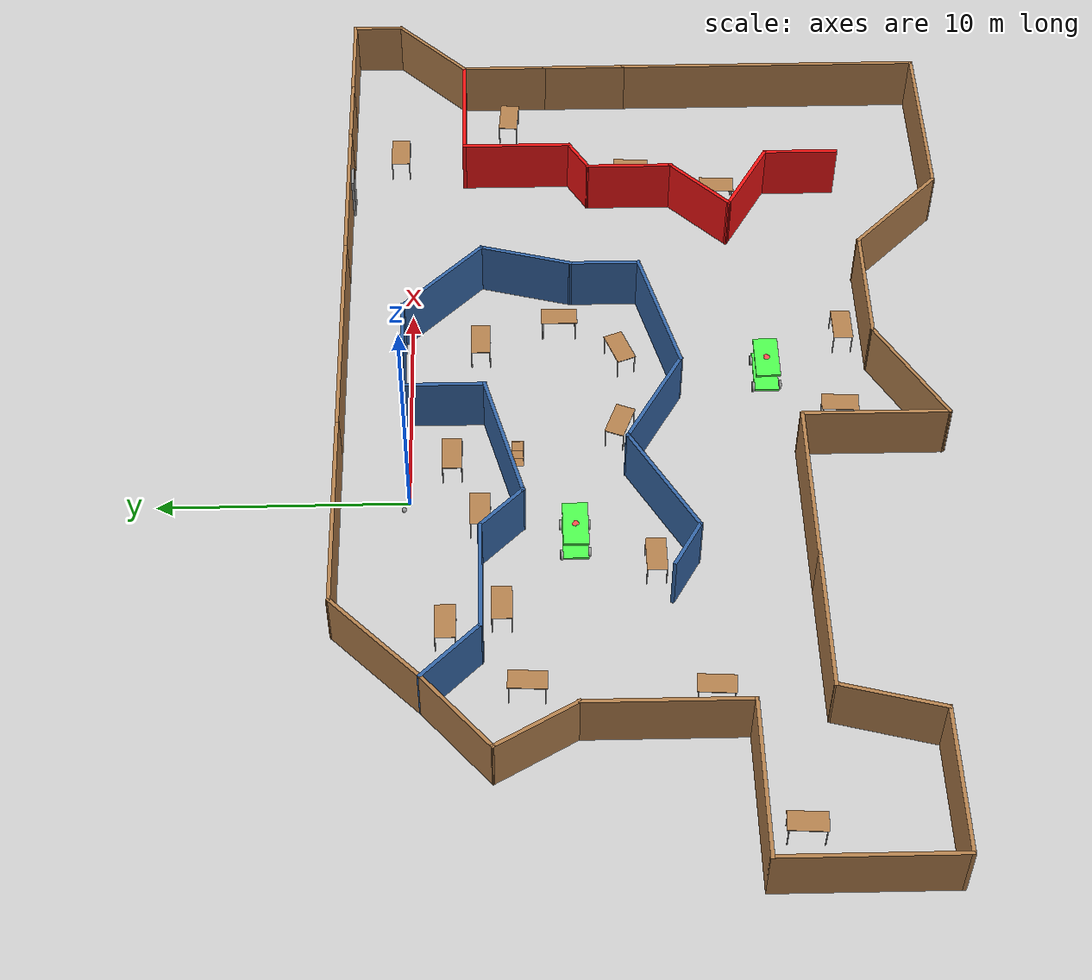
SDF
<sdf version="1.6">
 <world name="default">
  <plugin name="worldhellow" filename="libworldhellow.so"/>
  <light name="sun" type="directional">
   <pose>0 0 10 0 -0 0</pose>
   <diffuse>0.8 0.8 0.8 1</diffuse>
   <specular>0.2 0.2 0.2 1</specular>
   <attenuation>
    <range>1000</range>
    <constant>0.9</constant>
    <linear>0.01</linear>
    <quadratic>0.001</quadratic>
   </attenuation>
   <direction>-0.5 0.1 -0.9</direction>
  </light>
  <model name="ground_plane">
   <static>1</static>
   <link name="link">
    <collision name="collision">
     <geometry><plane><normal>0 0 1</normal><size>100 100</size></plane></geometry>
     <surface>
      <contact><collide_bitmask>65535</collide_bitmask></contact>
      <friction><ode><mu>100</mu><mu2>50</mu2></ode></friction>
     </surface>
    </collision>
    <visual name="visual">
     <cast_shadows>0</cast_shadows>
     <geometry><plane><normal>0 0 1</normal><size>100 100</size></plane></geometry>
     <material>
      <script><uri>file://media/materials/scripts/gazebo.material</uri><name>Gazebo/Grey</name></script>
     </material>
    </visual>
   </link>
  </model>
  <gravity>0 0 -9.8</gravity>
  <magnetic_field>6e-06 2.3e-05 -4.2e-05</magnetic_field>
  <atmosphere type="adiabatic"/>
  <physics name="default_physics" default="0" type="ode">
   <max_step_size>0.001</max_step_size>
   <real_time_factor>1</real_time_factor>
   <real_time_update_rate>1000</real_time_update_rate>
  </physics>
  <scene><ambient>0.4 0.4 0.4 1</ambient><background>0.7 0.7 0.7 1</background><shadows>1</shadows></scene>
  <spherical_coordinates>
   <surface_model>EARTH_WGS84</surface_model>
   <latitude_deg>0</latitude_deg>
   <longitude_deg>0</longitude_deg>
   <elevation>0</elevation>
   <heading_deg>0</heading_deg>
  </spherical_coordinates>
  <model name="office_0">
   <pose>4.3391 -9.8283 0 0 -0 0</pose>
   <link name="Door_0">
    <collision name="Door_0_Collision">
     <geometry><box><size>0.9 0.17 2</size></box></geometry>
     <pose>0 0 1 0 -0 0</pose>
    </collision>
    <visual name="Door_0_Visual">
     <pose>0 0 1 0 -0 0</pose>
     <geometry><box><size>0.9 0.17 2</size></box></geometry>
     <material>
      <script><uri>file://media/materials/scripts/gazebo.material</uri><name>Gazebo/Grey</name></script>
     </material>
    </visual>
    <pose>12.3308 12.5503 0 0 -0 0</pose>
   </link>
   <link name="Wall_0">
    <collision name="Wall_0_Collision">
     <geometry><box><size>5 0.15 2.5</size></box></geometry>
     <pose>0 0 1.25 0 -0 0</pose>
    </collision>
    <visual name="Wall_0_Visual">
     <pose>0 0 1.25 0 -0 0</pose>
     <geometry><box><size>5 0.15 2.5</size></box></geometry>
     <material>
      <script><uri>file://media/materials/scripts/gazebo.material</uri><name>Gazebo/Wood</name></script>
      <ambient>1 1 1 1</ambient>
     </material>
     <meta><layer>0</layer></meta>
    </visual>
    <pose>-12.3636 10.9348 0 0 -0 0.785398</pose>
   </link>
   <link name="Wall_1">
    <collision name="Wall_1_Collision">
     <geometry><box><size>8.75 0.15 2.5</size></box></geometry>
     <pose>0 0 1.25 0 -0 0</pose>
    </collision>
    <visual name="Wall_1_Visual">
     <pose>0 0 1.25 0 -0 0</pose>
     <geometry><box><size>8.75 0.15 2.5</size></box></geometry>
     <material>
      <script><uri>file://media/materials/scripts/gazebo.material</uri><name>Gazebo/Wood</name></script>
      <ambient>1 1 1 1</ambient>
     </material>
     <meta><layer>0</layer></meta>
    </visual>
    <pose>-6.3489 12.6496 0 0 -0 0</pose>
   </link>
   <link name="Wall_10">
    <collision name="Wall_10_Collision">
     <geometry><box><size>13.25 0.15 2.5</size></box></geometry>
     <pose>0 0 1.25 0 -0 0</pose>
    </collision>
    <visual name="Wall_10_Visual">
     <pose>0 0 1.25 0 -0 0</pose>
     <geometry><box><size>13.25 0.15 2.5</size></box></geometry>
     <material>
      <script><uri>file://media/materials/scripts/gazebo.material</uri><name>Gazebo/Wood</name></script>
      <ambient>1 1 1 1</ambient>
     </material>
     <meta><layer>0</layer></meta>
    </visual>
    <pose>18.702 -6.09957 0 0 -0 -1.5708</pose>
   </link>
   <link name="Wall_11">
    <collision name="Wall_11_Collision">
     <geometry><box><size>7.75 0.15 2.5</size></box></geometry>
     <pose>0 0 1.25 0 -0 0</pose>
    </collision>
    <visual name="Wall_11_Visual">
     <pose>0 0 1.25 0 -0 0</pose>
     <geometry><box><size>7.75 0.15 2.5</size></box></geometry>
     <material>
      <script><uri>file://media/materials/scripts/gazebo.material</uri><name>Gazebo/Wood</name></script>
      <ambient>1 1 1 1</ambient>
     </material>
     <meta><layer>0</layer></meta>
    </visual>
    <pose>14.902 -12.6496 0 0 -0 3.14159</pose>
   </link>
   <link name="Wall_12">
    <collision name="Wall_12_Collision">
     <geometry><box><size>5.25 0.15 2.5</size></box></geometry>
     <pose>0 0 1.25 0 -0 0</pose>
    </collision>
    <visual name="Wall_12_Visual">
     <pose>0 0 1.25 0 -0 0</pose>
     <geometry><box><size>5.25 0.15 2.5</size></box></geometry>
     <material>
      <script><uri>file://media/materials/scripts/gazebo.material</uri><name>Gazebo/Wood</name></script>
      <ambient>1 1 1 1</ambient>
     </material>
     <meta><layer>0</layer></meta>
    </visual>
    <pose>9.29884 -10.8464 0 0 -0 2.35619</pose>
   </link>
   <link name="Wall_13">
    <collision name="Wall_13_Collision">
     <geometry><box><size>5.25 0.15 2.5</size></box></geometry>
     <pose>0 0 1.25 0 -0 0</pose>
    </collision>
    <visual name="Wall_13_Visual">
     <pose>0 0 1.25 0 -0 0</pose>
     <geometry><box><size>5.25 0.15 2.5</size></box></geometry>
     <material>
      <script><uri>file://media/materials/scripts/gazebo.material</uri><name>Gazebo/Wood</name></script>
      <ambient>1 1 1 1</ambient>
     </material>
     <meta><layer>0</layer></meta>
    </visual>
    <pose>4.94572 -9.04332 0 0 -0 3.14159</pose>
   </link>
   <link name="Wall_14">
    <collision name="Wall_14_Collision">
     <geometry><box><size>5.25 0.15 2.5</size></box></geometry>
     <pose>0 0 1.25 0 -0 0</pose>
    </collision>
    <visual name="Wall_14_Visual">
     <pose>0 0 1.25 0 -0 0</pose>
     <geometry><box><size>5.25 0.15 2.5</size></box></geometry>
     <material>
      <script><uri>file://media/materials/scripts/gazebo.material</uri><name>Gazebo/Wood</name></script>
      <ambient>1 1 1 1</ambient>
     </material>
     <meta><layer>0</layer></meta>
    </visual>
    <pose>0.187355 -10.3183 0 0 -0 -2.61799</pose>
   </link>
   <link name="Wall_15">
    <collision name="Wall_15_Collision">
     <geometry><box><size>6 0.15 2.5</size></box></geometry>
     <pose>0 0 1.25 0 -0 0</pose>
    </collision>
    <visual name="Wall_15_Visual">
     <pose>0 0 1.25 0 -0 0</pose>
     <geometry><box><size>6 0.15 2.5</size></box></geometry>
     <material>
      <script><uri>file://media/materials/scripts/gazebo.material</uri><name>Gazebo/Wood</name></script>
      <ambient>1 1 1 1</ambient>
     </material>
     <meta><layer>0</layer></meta>
    </visual>
    <pose>-2.02101 -8.66832 0 0 -0 1.5708</pose>
   </link>
   <link name="Wall_16">
    <collision name="Wall_16_Collision">
     <geometry><box><size>7 0.15 2.5</size></box></geometry>
     <pose>0 0 1.25 0 -0 0</pose>
    </collision>
    <visual name="Wall_16_Visual">
     <pose>0 0 1.25 0 -0 0</pose>
     <geometry><box><size>7 0.15 2.5</size></box></geometry>
     <material>
      <script><uri>file://media/materials/scripts/gazebo.material</uri><name>Gazebo/Wood</name></script>
      <ambient>1 1 1 1</ambient>
     </material>
     <meta><layer>0</layer></meta>
    </visual>
    <pose>-5.44601 -5.74332 0 0 -0 3.14159</pose>
   </link>
   <link name="Wall_17">
    <collision name="Wall_17_Collision">
     <geometry><box><size>6 0.15 2.5</size></box></geometry>
     <pose>0 0 1.25 0 -0 0</pose>
    </collision>
    <visual name="Wall_17_Visual">
     <pose>0 0 1.25 0 -0 0</pose>
     <geometry><box><size>6 0.15 2.5</size></box></geometry>
     <material>
      <script><uri>file://media/materials/scripts/gazebo.material</uri><name>Gazebo/Wood</name></script>
      <ambient>1 1 1 1</ambient>
     </material>
     <meta><layer>0</layer></meta>
    </visual>
    <pose>-11.796 -5.74332 0 0 -0 3.14159</pose>
   </link>
   <link name="Wall_18">
    <collision name="Wall_18_Collision">
     <geometry><box><size>4.25 0.15 2.5</size></box></geometry>
     <pose>0 0 1.25 0 -0 0</pose>
    </collision>
    <visual name="Wall_18_Visual">
     <pose>0 0 1.25 0 -0 0</pose>
     <geometry><box><size>4.25 0.15 2.5</size></box></geometry>
     <material>
      <script><uri>file://media/materials/scripts/gazebo.material</uri><name>Gazebo/Wood</name></script>
      <ambient>1 1 1 1</ambient>
     </material>
     <meta><layer>0</layer></meta>
    </visual>
    <pose>-15.2516 -7.72347 0 0 -0 -1.8326</pose>
   </link>
   <link name="Wall_19">
    <collision name="Wall_19_Collision">
     <geometry><box><size>6 0.15 2.5</size></box></geometry>
     <pose>0 0 1.25 0 -0 0</pose>
    </collision>
    <visual name="Wall_19_Visual">
     <pose>0 0 1.25 0 -0 0</pose>
     <geometry><box><size>6 0.15 2.5</size></box></geometry>
     <material>
      <script><uri>file://media/materials/scripts/gazebo.material</uri><name>Gazebo/Wood</name></script>
      <ambient>1 1 1 1</ambient>
     </material>
     <meta><layer>0</layer></meta>
    </visual>
    <pose>-18.7072 -9.70362 0 0 -0 3.14159</pose>
   </link>
   <link name="Wall_2">
    <collision name="Wall_2_Collision">
     <geometry><box><size>9.75 0.15 2.5</size></box></geometry>
     <pose>0 0 1.25 0 -0 0</pose>
    </collision>
    <visual name="Wall_2_Visual">
     <pose>0 0 1.25 0 -0 0</pose>
     <geometry><box><size>9.75 0.15 2.5</size></box></geometry>
     <material>
      <script><uri>file://media/materials/scripts/gazebo.material</uri><name>Gazebo/Wood</name></script>
      <ambient>1 1 1 1</ambient>
     </material>
     <meta><layer>0</layer></meta>
    </visual>
    <pose>2.7511 12.6496 0 0 -0 0</pose>
   </link>
   <link name="Wall_20">
    <collision name="Wall_20_Collision">
     <geometry><box><size>7 0.15 2.5</size></box></geometry>
     <pose>0 0 1.25 0 -0 0</pose>
    </collision>
    <visual name="Wall_20_Visual">
     <pose>0 0 1.25 0 -0 0</pose>
     <geometry><box><size>7 0.15 2.5</size></box></geometry>
     <material>
      <script><uri>file://media/materials/scripts/gazebo.material</uri><name>Gazebo/Wood</name></script>
      <ambient>1 1 1 1</ambient>
     </material>
     <meta><layer>0</layer></meta>
    </visual>
    <pose>-21.6322 -6.27862 0 0 -0 1.5708</pose>
   </link>
   <link name="Wall_21">
    <collision name="Wall_21_Collision">
     <geometry><box><size>6.5 0.15 2.5</size></box></geometry>
     <pose>0 0 1.25 0 -0 0</pose>
    </collision>
    <visual name="Wall_21_Visual">
     <pose>0 0 1.25 0 -0 0</pose>
     <geometry><box><size>6.5 0.15 2.5</size></box></geometry>
     <material>
      <script><uri>file://media/materials/scripts/gazebo.material</uri><name>Gazebo/Wood</name></script>
      <ambient>1 1 1 1</ambient>
     </material>
     <meta><layer>0</layer></meta>
    </visual>
    <pose>-18.4572 -2.85362 0 0 -0 0</pose>
   </link>
   <link name="Wall_22">
    <collision name="Wall_22_Collision">
     <geometry><box><size>6.5 0.15 2.5</size></box></geometry>
     <pose>0 0 1.25 0 -0 0</pose>
    </collision>
    <visual name="Wall_22_Visual">
     <pose>0 0 1.25 0 -0 0</pose>
     <geometry><box><size>6.5 0.15 2.5</size></box></geometry>
     <material>
      <script><uri>file://media/materials/scripts/gazebo.material</uri><name>Gazebo/Wood</name></script>
      <ambient>1 1 1 1</ambient>
     </material>
     <meta><layer>0</layer></meta>
    </visual>
    <pose>-15.2822 0.32138 0 0 -0 1.5708</pose>
   </link>
   <link name="Wall_23">
    <collision name="Wall_23_Collision">
     <geometry><box><size>3.75 0.15 2.5</size></box></geometry>
     <pose>0 0 1.25 0 -0 0</pose>
    </collision>
    <visual name="Wall_23_Visual">
     <pose>0 0 1.25 0 -0 0</pose>
     <geometry><box><size>3.75 0.15 2.5</size></box></geometry>
     <material>
      <script><uri>file://media/materials/scripts/gazebo.material</uri><name>Gazebo/Wood</name></script>
      <ambient>1 1 1 1</ambient>
     </material>
     <meta><layer>0</layer></meta>
    </visual>
    <pose>-16.1822 5.05523 0 0 -0 2.0944</pose>
   </link>
   <link name="Wall_24">
    <collision name="Wall_24_Collision">
     <geometry><box><size>4.12671 0.15 2.5</size></box></geometry>
     <pose>0 0 1.25 0 -0 0</pose>
    </collision>
    <visual name="Wall_24_Visual">
     <pose>0 0 1.25 0 -0 0</pose>
     <geometry><box><size>4.12671 0.15 2.5</size></box></geometry>
     <material>
      <script><uri>file://media/materials/scripts/gazebo.material</uri><name>Gazebo/Wood</name></script>
      <ambient>1 1 1 1</ambient>
     </material>
     <meta><layer>0</layer></meta>
    </visual>
    <pose>-15.5803 7.91709 0 0 -0 0.71461</pose>
   </link>
   <link name="Wall_25">
    <collision name="Wall_25_Collision">
     <geometry><box><size>3.25 0.15 2.5</size></box></geometry>
     <pose>0 0 1.25 0 -0 0</pose>
    </collision>
    <visual name="Wall_25_Visual">
     <pose>0 0 1.25 0 -0 0</pose>
     <geometry><box><size>3.25 0.15 2.5</size></box></geometry>
     <material>
      <script><uri>file://media/materials/scripts/gazebo.material</uri><name>Gazebo/Grey</name></script>
      <ambient>0.203922 0.396078 0.643137 1</ambient>
     </material>
     <meta><layer>0</layer></meta>
    </visual>
    <pose>-12.9824 8.12409 0 0 -0 -0.785398</pose>
   </link>
   <link name="Wall_26">
    <collision name="Wall_26_Collision">
     <geometry><box><size>4.75 0.15 2.5</size></box></geometry>
     <pose>0 0 1.25 0 -0 0</pose>
    </collision>
    <visual name="Wall_26_Visual">
     <pose>0 0 1.25 0 -0 0</pose>
     <geometry><box><size>4.75 0.15 2.5</size></box></geometry>
     <material>
      <script><uri>file://media/materials/scripts/gazebo.material</uri><name>Gazebo/Grey</name></script>
      <ambient>0.203922 0.396078 0.643137 1</ambient>
     </material>
     <meta><layer>0</layer></meta>
    </visual>
    <pose>-9.58634 7.02807 0 0 -0 0</pose>
   </link>
   <link name="Wall_27">
    <collision name="Wall_27_Collision">
     <geometry><box><size>2.5 0.15 2.5</size></box></geometry>
     <pose>0 0 1.25 0 -0 0</pose>
    </collision>
    <visual name="Wall_27_Visual">
     <pose>0 0 1.25 0 -0 0</pose>
     <geometry><box><size>2.5 0.15 2.5</size></box></geometry>
     <material>
      <script><uri>file://media/materials/scripts/gazebo.material</uri><name>Gazebo/Grey</name></script>
      <ambient>0.203922 0.396078 0.643137 1</ambient>
     </material>
     <meta><layer>0</layer></meta>
    </visual>
    <pose>-6.45548 6.19722 0 0 -0 -0.785398</pose>
   </link>
   <link name="Wall_28">
    <collision name="Wall_28_Collision">
     <geometry><box><size>5.75 0.15 2.5</size></box></geometry>
     <pose>0 0 1.25 0 -0 0</pose>
    </collision>
    <visual name="Wall_28_Visual">
     <pose>0 0 1.25 0 -0 0</pose>
     <geometry><box><size>5.75 0.15 2.5</size></box></geometry>
     <material>
      <script><uri>file://media/materials/scripts/gazebo.material</uri><name>Gazebo/Grey</name></script>
      <ambient>0.203922 0.396078 0.643137 1</ambient>
     </material>
     <meta><layer>0</layer></meta>
    </visual>
    <pose>-2.92004 6.09106 0 0 -0 0.261799</pose>
   </link>
   <link name="Wall_29">
    <collision name="Wall_29_Collision">
     <geometry><box><size>3.5 0.15 2.5</size></box></geometry>
     <pose>0 0 1.25 0 -0 0</pose>
    </collision>
    <visual name="Wall_29_Visual">
     <pose>0 0 1.25 0 -0 0</pose>
     <geometry><box><size>3.5 0.15 2.5</size></box></geometry>
     <material>
      <script><uri>file://media/materials/scripts/gazebo.material</uri><name>Gazebo/Grey</name></script>
      <ambient>0.203922 0.396078 0.643137 1</ambient>
     </material>
     <meta><layer>0</layer></meta>
    </visual>
    <pose>-0.215449 8.49076 0 0 -0 1.5708</pose>
   </link>
   <link name="Wall_3">
    <collision name="Wall_3_Collision">
     <geometry><box><size>7 0.15 2.5</size></box></geometry>
     <pose>0 0 1.25 0 -0 0</pose>
    </collision>
    <visual name="Wall_3_Visual">
     <pose>0 0 1.25 0 -0 0</pose>
     <geometry><box><size>7 0.15 2.5</size></box></geometry>
     <material>
      <script><uri>file://media/materials/scripts/gazebo.material</uri><name>Gazebo/Wood</name></script>
      <ambient>1 1 1 1</ambient>
     </material>
     <meta><layer>0</layer></meta>
    </visual>
    <pose>10.9761 12.6496 0 0 -0 0</pose>
   </link>
   <link name="Wall_30">
    <collision name="Wall_30_Collision">
     <geometry><box><size>4.5 0.15 2.5</size></box></geometry>
     <pose>0 0 1.25 0 -0 0</pose>
    </collision>
    <visual name="Wall_30_Visual">
     <pose>0 0 1.25 0 -0 0</pose>
     <geometry><box><size>4.5 0.15 2.5</size></box></geometry>
     <material>
      <script><uri>file://media/materials/scripts/gazebo.material</uri><name>Gazebo/Grey</name></script>
      <ambient>0.203922 0.396078 0.643137 1</ambient>
     </material>
     <meta><layer>0</layer></meta>
    </visual>
    <pose>1.95955 10.1658 0 0 -0 0</pose>
   </link>
   <link name="Wall_31">
    <collision name="Wall_31_Collision">
     <geometry><box><size>4.75 0.15 2.5</size></box></geometry>
     <pose>0 0 1.25 0 -0 0</pose>
    </collision>
    <visual name="Wall_31_Visual">
     <pose>0 0 1.25 0 -0 0</pose>
     <geometry><box><size>4.75 0.15 2.5</size></box></geometry>
     <material>
      <script><uri>file://media/materials/scripts/gazebo.material</uri><name>Gazebo/Grey</name></script>
      <ambient>0.203922 0.396078 0.643137 1</ambient>
     </material>
     <meta><layer>0</layer></meta>
    </visual>
    <pose>5.7609 8.53941 0 0 -0 -0.785398</pose>
   </link>
   <link name="Wall_32">
    <collision name="Wall_32_Collision">
     <geometry><box><size>4 0.15 2.5</size></box></geometry>
     <pose>0 0 1.25 0 -0 0</pose>
    </collision>
    <visual name="Wall_32_Visual">
     <pose>0 0 1.25 0 -0 0</pose>
     <geometry><box><size>4 0.15 2.5</size></box></geometry>
     <material>
      <script><uri>file://media/materials/scripts/gazebo.material</uri><name>Gazebo/Grey</name></script>
      <ambient>0.203922 0.396078 0.643137 1</ambient>
     </material>
     <meta><layer>0</layer></meta>
    </visual>
    <pose>6.88901 5.05366 0 0 -0 -1.8326</pose>
   </link>
   <link name="Wall_33">
    <collision name="Wall_33_Collision">
     <geometry><box><size>3 0.15 2.5</size></box></geometry>
     <pose>0 0 1.25 0 -0 0</pose>
    </collision>
    <visual name="Wall_33_Visual">
     <pose>0 0 1.25 0 -0 0</pose>
     <geometry><box><size>3 0.15 2.5</size></box></geometry>
     <material>
      <script><uri>file://media/materials/scripts/gazebo.material</uri><name>Gazebo/Grey</name></script>
      <ambient>0.203922 0.396078 0.643137 1</ambient>
     </material>
     <meta><layer>0</layer></meta>
    </visual>
    <pose>6.39079 1.76925 0 0 -0 -1.5708</pose>
   </link>
   <link name="Wall_34">
    <collision name="Wall_34_Collision">
     <geometry><box><size>5.75 0.15 2.5</size></box></geometry>
     <pose>0 0 1.25 0 -0 0</pose>
    </collision>
    <visual name="Wall_34_Visual">
     <pose>0 0 1.25 0 -0 0</pose>
     <geometry><box><size>5.75 0.15 2.5</size></box></geometry>
     <material>
      <script><uri>file://media/materials/scripts/gazebo.material</uri><name>Gazebo/Grey</name></script>
      <ambient>0.203922 0.396078 0.643137 1</ambient>
     </material>
     <meta><layer>0</layer></meta>
    </visual>
    <pose>3.6862 -0.380443 0 0 -0 -2.87979</pose>
   </link>
   <link name="Wall_35">
    <collision name="Wall_35_Collision">
     <geometry><box><size>4.75 0.15 2.5</size></box></geometry>
     <pose>0 0 1.25 0 -0 0</pose>
    </collision>
    <visual name="Wall_35_Visual">
     <pose>0 0 1.25 0 -0 0</pose>
     <geometry><box><size>4.75 0.15 2.5</size></box></geometry>
     <material>
      <script><uri>file://media/materials/scripts/gazebo.material</uri><name>Gazebo/Grey</name></script>
      <ambient>0.203922 0.396078 0.643137 1</ambient>
     </material>
     <meta><layer>0</layer></meta>
    </visual>
    <pose>-1.01025 0.044864 0 0 -0 2.61799</pose>
   </link>
   <link name="Wall_36">
    <collision name="Wall_36_Collision">
     <geometry><box><size>5.25 0.15 2.5</size></box></geometry>
     <pose>0 0 1.25 0 -0 0</pose>
    </collision>
    <visual name="Wall_36_Visual">
     <pose>0 0 1.25 0 -0 0</pose>
     <geometry><box><size>5.25 0.15 2.5</size></box></geometry>
     <material>
      <script><uri>file://media/materials/scripts/gazebo.material</uri><name>Gazebo/Grey</name></script>
      <ambient>0.203922 0.396078 0.643137 1</ambient>
     </material>
     <meta><layer>0</layer></meta>
    </visual>
    <pose>-5.21048 -0.080136 0 0 -0 -2.61799</pose>
   </link>
   <link name="Wall_37">
    <collision name="Wall_37_Collision">
     <geometry><box><size>2.25 0.15 2.5</size></box></geometry>
     <pose>0 0 1.25 0 -0 0</pose>
    </collision>
    <visual name="Wall_37_Visual">
     <pose>0 0 1.25 0 -0 0</pose>
     <geometry><box><size>2.25 0.15 2.5</size></box></geometry>
     <material>
      <script><uri>file://media/materials/scripts/gazebo.material</uri><name>Gazebo/Grey</name></script>
      <ambient>0.203922 0.396078 0.643137 1</ambient>
     </material>
     <meta><layer>0</layer></meta>
    </visual>
    <pose>-8.32817 -0.830136 0 0 -0 2.61799</pose>
   </link>
   <link name="Wall_39">
    <collision name="Wall_39_Collision">
     <geometry><box><size>5.25 0.15 2.5</size></box></geometry>
     <pose>0 0 1.25 0 -0 0</pose>
    </collision>
    <visual name="Wall_39_Visual">
     <pose>0 0 1.25 0 -0 0</pose>
     <geometry><box><size>5.25 0.15 2.5</size></box></geometry>
     <material>
      <script><uri>file://media/materials/scripts/gazebo.material</uri><name>Gazebo/Grey</name></script>
      <ambient>0.945098 0.0745098 0.0745098 1</ambient>
     </material>
     <meta><layer>0</layer></meta>
    </visual>
    <pose>16.152 7.65043 0 0 -0 3.14159</pose>
   </link>
   <link name="Wall_4">
    <collision name="Wall_4_Collision">
     <geometry><box><size>3.25 0.15 2.5</size></box></geometry>
     <pose>0 0 1.25 0 -0 0</pose>
    </collision>
    <visual name="Wall_4_Visual">
     <pose>0 0 1.25 0 -0 0</pose>
     <geometry><box><size>3.25 0.15 2.5</size></box></geometry>
     <material>
      <script><uri>file://media/materials/scripts/gazebo.material</uri><name>Gazebo/Wood</name></script>
      <ambient>1 1 1 1</ambient>
     </material>
     <meta><layer>0</layer></meta>
    </visual>
    <pose>15.9511 12.6496 0 0 -0 0</pose>
   </link>
   <link name="Wall_40">
    <collision name="Wall_40_Collision">
     <geometry><box><size>4.75 0.15 2.5</size></box></geometry>
     <pose>0 0 1.25 0 -0 0</pose>
    </collision>
    <visual name="Wall_40_Visual">
     <pose>0 0 1.25 0 -0 0</pose>
     <geometry><box><size>4.75 0.15 2.5</size></box></geometry>
     <material>
      <script><uri>file://media/materials/scripts/gazebo.material</uri><name>Gazebo/Grey</name></script>
      <ambient>0.945098 0.0745098 0.0745098 1</ambient>
     </material>
     <meta><layer>0</layer></meta>
    </visual>
    <pose>13.602 5.35043 0 0 -0 -1.5708</pose>
   </link>
   <link name="Wall_41">
    <collision name="Wall_41_Collision">
     <geometry><box><size>1.75 0.15 2.5</size></box></geometry>
     <pose>0 0 1.25 0 -0 0</pose>
    </collision>
    <visual name="Wall_41_Visual">
     <pose>0 0 1.25 0 -0 0</pose>
     <geometry><box><size>1.75 0.15 2.5</size></box></geometry>
     <material>
      <script><uri>file://media/materials/scripts/gazebo.material</uri><name>Gazebo/Grey</name></script>
      <ambient>0.945098 0.0745098 0.0745098 1</ambient>
     </material>
     <meta><layer>0</layer></meta>
    </visual>
    <pose>12.9091 2.65043 0 0 -0 -2.61799</pose>
   </link>
   <link name="Wall_42">
    <collision name="Wall_42_Collision">
     <geometry><box><size>3.75 0.15 2.5</size></box></geometry>
     <pose>0 0 1.25 0 -0 0</pose>
    </collision>
    <visual name="Wall_42_Visual">
     <pose>0 0 1.25 0 -0 0</pose>
     <geometry><box><size>3.75 0.15 2.5</size></box></geometry>
     <material>
      <script><uri>file://media/materials/scripts/gazebo.material</uri><name>Gazebo/Grey</name></script>
      <ambient>0.945098 0.0745098 0.0745098 1</ambient>
     </material>
     <meta><layer>0</layer></meta>
    </visual>
    <pose>12.2163 0.450431 0 0 -0 -1.5708</pose>
   </link>
   <link name="Wall_43">
    <collision name="Wall_43_Collision">
     <geometry><box><size>3.5 0.15 2.5</size></box></geometry>
     <pose>0 0 1.25 0 -0 0</pose>
    </collision>
    <visual name="Wall_43_Visual">
     <pose>0 0 1.25 0 -0 0</pose>
     <geometry><box><size>3.5 0.15 2.5</size></box></geometry>
     <material>
      <script><uri>file://media/materials/scripts/gazebo.material</uri><name>Gazebo/Grey</name></script>
      <ambient>0.945098 0.0745098 0.0745098 1</ambient>
     </material>
     <meta><layer>0</layer></meta>
    </visual>
    <pose>11.0319 -2.53397 0 0 -0 -2.35619</pose>
   </link>
   <link name="Wall_44">
    <collision name="Wall_44_Collision">
     <geometry><box><size>3.75 0.15 2.5</size></box></geometry>
     <pose>0 0 1.25 0 -0 0</pose>
    </collision>
    <visual name="Wall_44_Visual">
     <pose>0 0 1.25 0 -0 0</pose>
     <geometry><box><size>3.75 0.15 2.5</size></box></geometry>
     <material>
      <script><uri>file://media/materials/scripts/gazebo.material</uri><name>Gazebo/Grey</name></script>
      <ambient>0.945098 0.0745098 0.0745098 1</ambient>
     </material>
     <meta><layer>0</layer></meta>
    </visual>
    <pose>11.4064 -4.61838 0 0 -0 -0.523599</pose>
   </link>
   <link name="Wall_45">
    <collision name="Wall_45_Collision">
     <geometry><box><size>3.25 0.15 2.5</size></box></geometry>
     <pose>0 0 1.25 0 -0 0</pose>
    </collision>
    <visual name="Wall_45_Visual">
     <pose>0 0 1.25 0 -0 0</pose>
     <geometry><box><size>3.25 0.15 2.5</size></box></geometry>
     <material>
      <script><uri>file://media/materials/scripts/gazebo.material</uri><name>Gazebo/Grey</name></script>
      <ambient>0.945098 0.0745098 0.0745098 1</ambient>
     </material>
     <meta><layer>0</layer></meta>
    </visual>
    <pose>12.9652 -7.06838 0 0 -0 -1.5708</pose>
   </link>
   <link name="Wall_5">
    <collision name="Wall_5_Collision">
     <geometry><box><size>4.25 0.15 2.5</size></box></geometry>
     <pose>0 0 1.25 0 -0 0</pose>
    </collision>
    <visual name="Wall_5_Visual">
     <pose>0 0 1.25 0 -0 0</pose>
     <geometry><box><size>4.25 0.15 2.5</size></box></geometry>
     <material>
      <script><uri>file://media/materials/scripts/gazebo.material</uri><name>Gazebo/Wood</name></script>
      <ambient>1 1 1 1</ambient>
     </material>
     <meta><layer>0</layer></meta>
    </visual>
    <pose>19.5511 12.6496 0 0 -0 0</pose>
   </link>
   <link name="Wall_6">
    <collision name="Wall_6_Collision">
     <geometry><box><size>2.25 0.15 2.5</size></box></geometry>
     <pose>0 0 1.25 0 -0 0</pose>
    </collision>
    <visual name="Wall_6_Visual">
     <pose>0 0 1.25 0 -0 0</pose>
     <geometry><box><size>2.25 0.15 2.5</size></box></geometry>
     <material>
      <script><uri>file://media/materials/scripts/gazebo.material</uri><name>Gazebo/Wood</name></script>
      <ambient>1 1 1 1</ambient>
     </material>
     <meta><layer>0</layer></meta>
    </visual>
    <pose>21.6011 11.5996 0 0 -0 -1.5708</pose>
   </link>
   <link name="Wall_7">
    <collision name="Wall_7_Collision">
     <geometry><box><size>4.25 0.15 2.5</size></box></geometry>
     <pose>0 0 1.25 0 -0 0</pose>
    </collision>
    <visual name="Wall_7_Visual">
     <pose>0 0 1.25 0 -0 0</pose>
     <geometry><box><size>4.25 0.15 2.5</size></box></geometry>
     <material>
      <script><uri>file://media/materials/scripts/gazebo.material</uri><name>Gazebo/Wood</name></script>
      <ambient>1 1 1 1</ambient>
     </material>
     <meta><layer>0</layer></meta>
    </visual>
    <pose>20.1515 9.1 0 0 -0 -2.35619</pose>
   </link>
   <link name="Wall_8">
    <collision name="Wall_8_Collision">
     <geometry><box><size>3.75 0.15 2.5</size></box></geometry>
     <pose>0 0 1.25 0 -0 0</pose>
    </collision>
    <visual name="Wall_8_Visual">
     <pose>0 0 1.25 0 -0 0</pose>
     <geometry><box><size>3.75 0.15 2.5</size></box></geometry>
     <material>
      <script><uri>file://media/materials/scripts/gazebo.material</uri><name>Gazebo/Wood</name></script>
      <ambient>1 1 1 1</ambient>
     </material>
     <meta><layer>0</layer></meta>
    </visual>
    <pose>18.702 5.85043 0 0 -0 -1.5708</pose>
   </link>
   <link name="Wall_9">
    <collision name="Wall_9_Collision">
     <geometry><box><size>3.75 0.15 2.5</size></box></geometry>
     <pose>0 0 1.25 0 -0 0</pose>
    </collision>
    <visual name="Wall_9_Visual">
     <pose>0 0 1.25 0 -0 0</pose>
     <geometry><box><size>3.75 0.15 2.5</size></box></geometry>
     <material>
      <script><uri>file://media/materials/scripts/gazebo.material</uri><name>Gazebo/Wood</name></script>
      <ambient>1 1 1 1</ambient>
     </material>
     <meta><layer>0</layer></meta>
    </visual>
    <pose>18.702 2.25043 0 0 -0 -1.5708</pose>
   </link>
   <static>1</static>
  </model>
  <model name="cabinet">
   <static>1</static>
   <link name="cabinet_bottom_plate">
    <inertial>
     <pose>0 0 -1 0 -0 0</pose>
     <inertia><ixx>2.05</ixx><ixy>0</ixy><ixz>0</ixz><iyy>2.05</iyy><iyz>0</iyz><izz>2.05</izz></inertia>
     <mass>25</mass>
    </inertial>
    <collision name="cabinet_bottom_plate_geom">
     <pose>0 0 0.01 0 -0 0</pose>
     <geometry><box><size>0.45 0.45 0.02</size></box></geometry>
    </collision>
    <visual name="cabinet_bottom_plate_geom_visual">
     <pose>0 0 0.01 0 -0 0</pose>
     <geometry><box><size>0.45 0.45 0.02</size></box></geometry>
     <material>
      <script><uri>file://media/materials/scripts/gazebo.material</uri><name>Gazebo/Wood</name></script>
     </material>
    </visual>
    <collision name="cabinet_bottom_plate_geom_cabinet_back_plate">
     <pose>0.235 0 0.51 0 -0 0</pose>
     <geometry><box><size>0.02 0.45 1.02</size></box></geometry>
    </collision>
    <visual name="cabinet_bottom_plate_geom_cabinet_back_plate_visual">
     <pose>0.235 0 0.51 0 -0 0</pose>
     <geometry><box><size>0.02 0.45 1.02</size></box></geometry>
     <material>
      <script><uri>file://media/materials/scripts/gazebo.material</uri><name>Gazebo/Wood</name></script>
     </material>
    </visual>
    <collision name="cabinet_bottom_plate_geom_cabinet_left_plate">
     <pose>0 0.235 0.51 0 -0 0</pose>
     <geometry><box><size>0.45 0.02 1.02</size></box></geometry>
    </collision>
    <visual name="cabinet_bottom_plate_geom_cabinet_left_plate_visual">
     <pose>0 0.235 0.51 0 -0 0</pose>
     <geometry><box><size>0.45 0.02 1.02</size></box></geometry>
     <material>
      <script><uri>file://media/materials/scripts/gazebo.material</uri><name>Gazebo/Wood</name></script>
     </material>
    </visual>
    <collision name="cabinet_bottom_plate_geom_cabinet_middle_plate">
     <pose>0 0 0.51 0 -0 0</pose>
     <geometry><box><size>0.45 0.45 0.02</size></box></geometry>
    </collision>
    <visual name="cabinet_bottom_plate_geom_cabinet_middle_plate_visual">
     <pose>0 0 0.51 0 -0 0</pose>
     <geometry><box><size>0.45 0.45 0.02</size></box></geometry>
     <material>
      <script><uri>file://media/materials/scripts/gazebo.material</uri><name>Gazebo/Wood</name></script>
     </material>
    </visual>
    <collision name="cabinet_bottom_plate_geom_cabinet_right_plate">
     <pose>0 -0.235 0.51 0 -0 0</pose>
     <geometry><box><size>0.45 0.02 1.02</size></box></geometry>
    </collision>
    <visual name="cabinet_bottom_plate_geom_cabinet_right_plate_visual">
     <pose>0 -0.235 0.51 0 -0 0</pose>
     <geometry><box><size>0.45 0.02 1.02</size></box></geometry>
     <material>
      <script><uri>file://media/materials/scripts/gazebo.material</uri><name>Gazebo/Wood</name></script>
     </material>
    </visual>
    <collision name="cabinet_bottom_plate_geom_cabinet_top_plate">
     <pose>0 0 1.01 0 -0 0</pose>
     <geometry><box><size>0.45 0.45 0.02</size></box></geometry>
    </collision>
    <visual name="cabinet_bottom_plate_geom_cabinet_top_plate_visual">
     <pose>0 0 1.01 0 -0 0</pose>
     <geometry><box><size>0.45 0.45 0.02</size></box></geometry>
     <material>
      <script><uri>file://media/materials/scripts/gazebo.material</uri><name>Gazebo/Wood</name></script>
     </material>
    </visual>
   </link>
   <pose>2.07402 -4.29667 0 0 -0 0</pose>
  </model>
  <model name="table">
   <static>1</static>
   <link name="link">
    <collision name="surface">
     <pose>0 0 1 0 -0 0</pose>
     <geometry><box><size>1.5 0.8 0.03</size></box></geometry>
     <surface><friction><ode><mu>0.6</mu><mu2>0.6</mu2></ode></friction></surface>
    </collision>
    <visual name="visual1">
     <pose>0 0 1 0 -0 0</pose>
     <geometry><box><size>1.5 0.8 0.03</size></box></geometry>
     <material>
      <script><uri>file://media/materials/scripts/gazebo.material</uri><name>Gazebo/Wood</name></script>
     </material>
    </visual>
    <collision name="front_left_leg">
     <pose>0.68 0.38 0.5 0 -0 0</pose>
     <geometry><cylinder><radius>0.02</radius><length>1</length></cylinder></geometry>
    </collision>
    <visual name="front_left_leg">
     <pose>0.68 0.38 0.5 0 -0 0</pose>
     <geometry><cylinder><radius>0.02</radius><length>1</length></cylinder></geometry>
     <material>
      <script><uri>file://media/materials/scripts/gazebo.material</uri><name>Gazebo/Grey</name></script>
     </material>
    </visual>
    <collision name="front_right_leg">
     <pose>0.68 -0.38 0.5 0 -0 0</pose>
     <geometry><cylinder><radius>0.02</radius><length>1</length></cylinder></geometry>
    </collision>
    <visual name="front_right_leg">
     <pose>0.68 -0.38 0.5 0 -0 0</pose>
     <geometry><cylinder><radius>0.02</radius><length>1</length></cylinder></geometry>
     <material>
      <script><uri>file://media/materials/scripts/gazebo.material</uri><name>Gazebo/Grey</name></script>
     </material>
    </visual>
    <collision name="back_right_leg">
     <pose>-0.68 -0.38 0.5 0 -0 0</pose>
     <geometry><cylinder><radius>0.02</radius><length>1</length></cylinder></geometry>
    </collision>
    <visual name="back_right_leg">
     <pose>-0.68 -0.38 0.5 0 -0 0</pose>
     <geometry><cylinder><radius>0.02</radius><length>1</length></cylinder></geometry>
     <material>
      <script><uri>file://media/materials/scripts/gazebo.material</uri><name>Gazebo/Grey</name></script>
     </material>
    </visual>
    <collision name="back_left_leg">
     <pose>-0.68 0.38 0.5 0 -0 0</pose>
     <geometry><cylinder><radius>0.02</radius><length>1</length></cylinder></geometry>
    </collision>
    <visual name="back_left_leg">
     <pose>-0.68 0.38 0.5 0 -0 0</pose>
     <geometry><cylinder><radius>0.02</radius><length>1</length></cylinder></geometry>
     <material>
      <script><uri>file://media/materials/scripts/gazebo.material</uri><name>Gazebo/Grey</name></script>
     </material>
    </visual>
   </link>
   <pose>-5.5188 -3.58842 0 0 -0 0</pose>
  </model>
  <model name="table_clone">
   <static>1</static>
   <link name="link">
    <collision name="surface">
     <pose>0 0 1 0 -0 0</pose>
     <geometry><box><size>1.5 0.8 0.03</size></box></geometry>
     <surface><friction><ode><mu>0.6</mu><mu2>0.6</mu2></ode></friction></surface>
    </collision>
    <visual name="visual1">
     <pose>0 0 1 0 -0 0</pose>
     <geometry><box><size>1.5 0.8 0.03</size></box></geometry>
     <material>
      <script><uri>file://media/materials/scripts/gazebo.material</uri><name>Gazebo/Wood</name></script>
     </material>
    </visual>
    <collision name="front_left_leg">
     <pose>0.68 0.38 0.5 0 -0 0</pose>
     <geometry><cylinder><radius>0.02</radius><length>1</length></cylinder></geometry>
    </collision>
    <visual name="front_left_leg">
     <pose>0.68 0.38 0.5 0 -0 0</pose>
     <geometry><cylinder><radius>0.02</radius><length>1</length></cylinder></geometry>
     <material>
      <script><uri>file://media/materials/scripts/gazebo.material</uri><name>Gazebo/Grey</name></script>
     </material>
    </visual>
    <collision name="front_right_leg">
     <pose>0.68 -0.38 0.5 0 -0 0</pose>
     <geometry><cylinder><radius>0.02</radius><length>1</length></cylinder></geometry>
    </collision>
    <visual name="front_right_leg">
     <pose>0.68 -0.38 0.5 0 -0 0</pose>
     <geometry><cylinder><radius>0.02</radius><length>1</length></cylinder></geometry>
     <material>
      <script><uri>file://media/materials/scripts/gazebo.material</uri><name>Gazebo/Grey</name></script>
     </material>
    </visual>
    <collision name="back_right_leg">
     <pose>-0.68 -0.38 0.5 0 -0 0</pose>
     <geometry><cylinder><radius>0.02</radius><length>1</length></cylinder></geometry>
    </collision>
    <visual name="back_right_leg">
     <pose>-0.68 -0.38 0.5 0 -0 0</pose>
     <geometry><cylinder><radius>0.02</radius><length>1</length></cylinder></geometry>
     <material>
      <script><uri>file://media/materials/scripts/gazebo.material</uri><name>Gazebo/Grey</name></script>
     </material>
    </visual>
    <collision name="back_left_leg">
     <pose>-0.68 0.38 0.5 0 -0 0</pose>
     <geometry><cylinder><radius>0.02</radius><length>1</length></cylinder></geometry>
    </collision>
    <visual name="back_left_leg">
     <pose>-0.68 0.38 0.5 0 -0 0</pose>
     <geometry><cylinder><radius>0.02</radius><length>1</length></cylinder></geometry>
     <material>
      <script><uri>file://media/materials/scripts/gazebo.material</uri><name>Gazebo/Grey</name></script>
     </material>
    </visual>
   </link>
   <pose>-3.37257 -9.55007 0 0 -0 0</pose>
  </model>
  <model name="table_clone_0">
   <static>1</static>
   <link name="link">
    <collision name="surface">
     <pose>0 0 1 0 -0 0</pose>
     <geometry><box><size>1.5 0.8 0.03</size></box></geometry>
     <surface><friction><ode><mu>0.6</mu><mu2>0.6</mu2></ode></friction></surface>
    </collision>
    <visual name="visual1">
     <pose>0 0 1 0 -0 0</pose>
     <geometry><box><size>1.5 0.8 0.03</size></box></geometry>
     <material>
      <script><uri>file://media/materials/scripts/gazebo.material</uri><name>Gazebo/Wood</name></script>
     </material>
    </visual>
    <collision name="front_left_leg">
     <pose>0.68 0.38 0.5 0 -0 0</pose>
     <geometry><cylinder><radius>0.02</radius><length>1</length></cylinder></geometry>
    </collision>
    <visual name="front_left_leg">
     <pose>0.68 0.38 0.5 0 -0 0</pose>
     <geometry><cylinder><radius>0.02</radius><length>1</length></cylinder></geometry>
     <material>
      <script><uri>file://media/materials/scripts/gazebo.material</uri><name>Gazebo/Grey</name></script>
     </material>
    </visual>
    <collision name="front_right_leg">
     <pose>0.68 -0.38 0.5 0 -0 0</pose>
     <geometry><cylinder><radius>0.02</radius><length>1</length></cylinder></geometry>
    </collision>
    <visual name="front_right_leg">
     <pose>0.68 -0.38 0.5 0 -0 0</pose>
     <geometry><cylinder><radius>0.02</radius><length>1</length></cylinder></geometry>
     <material>
      <script><uri>file://media/materials/scripts/gazebo.material</uri><name>Gazebo/Grey</name></script>
     </material>
    </visual>
    <collision name="back_right_leg">
     <pose>-0.68 -0.38 0.5 0 -0 0</pose>
     <geometry><cylinder><radius>0.02</radius><length>1</length></cylinder></geometry>
    </collision>
    <visual name="back_right_leg">
     <pose>-0.68 -0.38 0.5 0 -0 0</pose>
     <geometry><cylinder><radius>0.02</radius><length>1</length></cylinder></geometry>
     <material>
      <script><uri>file://media/materials/scripts/gazebo.material</uri><name>Gazebo/Grey</name></script>
     </material>
    </visual>
    <collision name="back_left_leg">
     <pose>-0.68 0.38 0.5 0 -0 0</pose>
     <geometry><cylinder><radius>0.02</radius><length>1</length></cylinder></geometry>
    </collision>
    <visual name="back_left_leg">
     <pose>-0.68 0.38 0.5 0 -0 0</pose>
     <geometry><cylinder><radius>0.02</radius><length>1</length></cylinder></geometry>
     <material>
      <script><uri>file://media/materials/scripts/gazebo.material</uri><name>Gazebo/Grey</name></script>
     </material>
    </visual>
   </link>
   <pose>3.34853 -8.43723 0 0 0 -0.370009</pose>
  </model>
  <model name="table_clone_1">
   <static>1</static>
   <link name="link">
    <collision name="surface">
     <pose>0 0 1 0 -0 0</pose>
     <geometry><box><size>1.5 0.8 0.03</size></box></geometry>
     <surface><friction><ode><mu>0.6</mu><mu2>0.6</mu2></ode></friction></surface>
    </collision>
    <visual name="visual1">
     <pose>0 0 1 0 -0 0</pose>
     <geometry><box><size>1.5 0.8 0.03</size></box></geometry>
     <material>
      <script><uri>file://media/materials/scripts/gazebo.material</uri><name>Gazebo/Wood</name></script>
     </material>
    </visual>
    <collision name="front_left_leg">
     <pose>0.68 0.38 0.5 0 -0 0</pose>
     <geometry><cylinder><radius>0.02</radius><length>1</length></cylinder></geometry>
    </collision>
    <visual name="front_left_leg">
     <pose>0.68 0.38 0.5 0 -0 0</pose>
     <geometry><cylinder><radius>0.02</radius><length>1</length></cylinder></geometry>
     <material>
      <script><uri>file://media/materials/scripts/gazebo.material</uri><name>Gazebo/Grey</name></script>
     </material>
    </visual>
    <collision name="front_right_leg">
     <pose>0.68 -0.38 0.5 0 -0 0</pose>
     <geometry><cylinder><radius>0.02</radius><length>1</length></cylinder></geometry>
    </collision>
    <visual name="front_right_leg">
     <pose>0.68 -0.38 0.5 0 -0 0</pose>
     <geometry><cylinder><radius>0.02</radius><length>1</length></cylinder></geometry>
     <material>
      <script><uri>file://media/materials/scripts/gazebo.material</uri><name>Gazebo/Grey</name></script>
     </material>
    </visual>
    <collision name="back_right_leg">
     <pose>-0.68 -0.38 0.5 0 -0 0</pose>
     <geometry><cylinder><radius>0.02</radius><length>1</length></cylinder></geometry>
    </collision>
    <visual name="back_right_leg">
     <pose>-0.68 -0.38 0.5 0 -0 0</pose>
     <geometry><cylinder><radius>0.02</radius><length>1</length></cylinder></geometry>
     <material>
      <script><uri>file://media/materials/scripts/gazebo.material</uri><name>Gazebo/Grey</name></script>
     </material>
    </visual>
    <collision name="back_left_leg">
     <pose>-0.68 0.38 0.5 0 -0 0</pose>
     <geometry><cylinder><radius>0.02</radius><length>1</length></cylinder></geometry>
    </collision>
    <visual name="back_left_leg">
     <pose>-0.68 0.38 0.5 0 -0 0</pose>
     <geometry><cylinder><radius>0.02</radius><length>1</length></cylinder></geometry>
     <material>
      <script><uri>file://media/materials/scripts/gazebo.material</uri><name>Gazebo/Grey</name></script>
     </material>
    </visual>
   </link>
   <pose>7.30475 -8.59495 0 -0.003044 -0.007938 0.366147</pose>
  </model>
  <model name="table_clone_2">
   <static>1</static>
   <link name="link">
    <collision name="surface">
     <pose>0 0 1 0 -0 0</pose>
     <geometry><box><size>1.5 0.8 0.03</size></box></geometry>
     <surface><friction><ode><mu>0.6</mu><mu2>0.6</mu2></ode></friction></surface>
    </collision>
    <visual name="visual1">
     <pose>0 0 1 0 -0 0</pose>
     <geometry><box><size>1.5 0.8 0.03</size></box></geometry>
     <material>
      <script><uri>file://media/materials/scripts/gazebo.material</uri><name>Gazebo/Wood</name></script>
     </material>
    </visual>
    <collision name="front_left_leg">
     <pose>0.68 0.38 0.5 0 -0 0</pose>
     <geometry><cylinder><radius>0.02</radius><length>1</length></cylinder></geometry>
    </collision>
    <visual name="front_left_leg">
     <pose>0.68 0.38 0.5 0 -0 0</pose>
     <geometry><cylinder><radius>0.02</radius><length>1</length></cylinder></geometry>
     <material>
      <script><uri>file://media/materials/scripts/gazebo.material</uri><name>Gazebo/Grey</name></script>
     </material>
    </visual>
    <collision name="front_right_leg">
     <pose>0.68 -0.38 0.5 0 -0 0</pose>
     <geometry><cylinder><radius>0.02</radius><length>1</length></cylinder></geometry>
    </collision>
    <visual name="front_right_leg">
     <pose>0.68 -0.38 0.5 0 -0 0</pose>
     <geometry><cylinder><radius>0.02</radius><length>1</length></cylinder></geometry>
     <material>
      <script><uri>file://media/materials/scripts/gazebo.material</uri><name>Gazebo/Grey</name></script>
     </material>
    </visual>
    <collision name="back_right_leg">
     <pose>-0.68 -0.38 0.5 0 -0 0</pose>
     <geometry><cylinder><radius>0.02</radius><length>1</length></cylinder></geometry>
    </collision>
    <visual name="back_right_leg">
     <pose>-0.68 -0.38 0.5 0 -0 0</pose>
     <geometry><cylinder><radius>0.02</radius><length>1</length></cylinder></geometry>
     <material>
      <script><uri>file://media/materials/scripts/gazebo.material</uri><name>Gazebo/Grey</name></script>
     </material>
    </visual>
    <collision name="back_left_leg">
     <pose>-0.68 0.38 0.5 0 -0 0</pose>
     <geometry><cylinder><radius>0.02</radius><length>1</length></cylinder></geometry>
    </collision>
    <visual name="back_left_leg">
     <pose>-0.68 0.38 0.5 0 -0 0</pose>
     <geometry><cylinder><radius>0.02</radius><length>1</length></cylinder></geometry>
     <material>
      <script><uri>file://media/materials/scripts/gazebo.material</uri><name>Gazebo/Grey</name></script>
     </material>
    </visual>
   </link>
   <pose>9.06126 -6.12559 0 0 -0 1.56558</pose>
  </model>
  <model name="table_clone_3">
   <static>1</static>
   <link name="link">
    <collision name="surface">
     <pose>0 0 1 0 -0 0</pose>
     <geometry><box><size>1.5 0.8 0.03</size></box></geometry>
     <surface><friction><ode><mu>0.6</mu><mu2>0.6</mu2></ode></friction></surface>
    </collision>
    <visual name="visual1">
     <pose>0 0 1 0 -0 0</pose>
     <geometry><box><size>1.5 0.8 0.03</size></box></geometry>
     <material>
      <script><uri>file://media/materials/scripts/gazebo.material</uri><name>Gazebo/Wood</name></script>
     </material>
    </visual>
    <collision name="front_left_leg">
     <pose>0.68 0.38 0.5 0 -0 0</pose>
     <geometry><cylinder><radius>0.02</radius><length>1</length></cylinder></geometry>
    </collision>
    <visual name="front_left_leg">
     <pose>0.68 0.38 0.5 0 -0 0</pose>
     <geometry><cylinder><radius>0.02</radius><length>1</length></cylinder></geometry>
     <material>
      <script><uri>file://media/materials/scripts/gazebo.material</uri><name>Gazebo/Grey</name></script>
     </material>
    </visual>
    <collision name="front_right_leg">
     <pose>0.68 -0.38 0.5 0 -0 0</pose>
     <geometry><cylinder><radius>0.02</radius><length>1</length></cylinder></geometry>
    </collision>
    <visual name="front_right_leg">
     <pose>0.68 -0.38 0.5 0 -0 0</pose>
     <geometry><cylinder><radius>0.02</radius><length>1</length></cylinder></geometry>
     <material>
      <script><uri>file://media/materials/scripts/gazebo.material</uri><name>Gazebo/Grey</name></script>
     </material>
    </visual>
    <collision name="back_right_leg">
     <pose>-0.68 -0.38 0.5 0 -0 0</pose>
     <geometry><cylinder><radius>0.02</radius><length>1</length></cylinder></geometry>
    </collision>
    <visual name="back_right_leg">
     <pose>-0.68 -0.38 0.5 0 -0 0</pose>
     <geometry><cylinder><radius>0.02</radius><length>1</length></cylinder></geometry>
     <material>
      <script><uri>file://media/materials/scripts/gazebo.material</uri><name>Gazebo/Grey</name></script>
     </material>
    </visual>
    <collision name="back_left_leg">
     <pose>-0.68 0.38 0.5 0 -0 0</pose>
     <geometry><cylinder><radius>0.02</radius><length>1</length></cylinder></geometry>
    </collision>
    <visual name="back_left_leg">
     <pose>-0.68 0.38 0.5 0 -0 0</pose>
     <geometry><cylinder><radius>0.02</radius><length>1</length></cylinder></geometry>
     <material>
      <script><uri>file://media/materials/scripts/gazebo.material</uri><name>Gazebo/Grey</name></script>
     </material>
    </visual>
   </link>
   <pose>7.84177 -2.84617 0 0 -0 0</pose>
  </model>
  <model name="table_clone_4">
   <static>1</static>
   <link name="link">
    <collision name="surface">
     <pose>0 0 1 0 -0 0</pose>
     <geometry><box><size>1.5 0.8 0.03</size></box></geometry>
     <surface><friction><ode><mu>0.6</mu><mu2>0.6</mu2></ode></friction></surface>
    </collision>
    <visual name="visual1">
     <pose>0 0 1 0 -0 0</pose>
     <geometry><box><size>1.5 0.8 0.03</size></box></geometry>
     <material>
      <script><uri>file://media/materials/scripts/gazebo.material</uri><name>Gazebo/Wood</name></script>
     </material>
    </visual>
    <collision name="front_left_leg">
     <pose>0.68 0.38 0.5 0 -0 0</pose>
     <geometry><cylinder><radius>0.02</radius><length>1</length></cylinder></geometry>
    </collision>
    <visual name="front_left_leg">
     <pose>0.68 0.38 0.5 0 -0 0</pose>
     <geometry><cylinder><radius>0.02</radius><length>1</length></cylinder></geometry>
     <material>
      <script><uri>file://media/materials/scripts/gazebo.material</uri><name>Gazebo/Grey</name></script>
     </material>
    </visual>
    <collision name="front_right_leg">
     <pose>0.68 -0.38 0.5 0 -0 0</pose>
     <geometry><cylinder><radius>0.02</radius><length>1</length></cylinder></geometry>
    </collision>
    <visual name="front_right_leg">
     <pose>0.68 -0.38 0.5 0 -0 0</pose>
     <geometry><cylinder><radius>0.02</radius><length>1</length></cylinder></geometry>
     <material>
      <script><uri>file://media/materials/scripts/gazebo.material</uri><name>Gazebo/Grey</name></script>
     </material>
    </visual>
    <collision name="back_right_leg">
     <pose>-0.68 -0.38 0.5 0 -0 0</pose>
     <geometry><cylinder><radius>0.02</radius><length>1</length></cylinder></geometry>
    </collision>
    <visual name="back_right_leg">
     <pose>-0.68 -0.38 0.5 0 -0 0</pose>
     <geometry><cylinder><radius>0.02</radius><length>1</length></cylinder></geometry>
     <material>
      <script><uri>file://media/materials/scripts/gazebo.material</uri><name>Gazebo/Grey</name></script>
     </material>
    </visual>
    <collision name="back_left_leg">
     <pose>-0.68 0.38 0.5 0 -0 0</pose>
     <geometry><cylinder><radius>0.02</radius><length>1</length></cylinder></geometry>
    </collision>
    <visual name="back_left_leg">
     <pose>-0.68 0.38 0.5 0 -0 0</pose>
     <geometry><cylinder><radius>0.02</radius><length>1</length></cylinder></geometry>
     <material>
      <script><uri>file://media/materials/scripts/gazebo.material</uri><name>Gazebo/Grey</name></script>
     </material>
    </visual>
   </link>
   <pose>-6.33417 -1.44501 0 0 -0 0</pose>
  </model>
  <model name="table_clone_5">
   <static>1</static>
   <link name="link">
    <collision name="surface">
     <pose>0 0 1 0 -0 0</pose>
     <geometry><box><size>1.5 0.8 0.03</size></box></geometry>
     <surface><friction><ode><mu>0.6</mu><mu2>0.6</mu2></ode></friction></surface>
    </collision>
    <visual name="visual1">
     <pose>0 0 1 0 -0 0</pose>
     <geometry><box><size>1.5 0.8 0.03</size></box></geometry>
     <material>
      <script><uri>file://media/materials/scripts/gazebo.material</uri><name>Gazebo/Wood</name></script>
     </material>
    </visual>
    <collision name="front_left_leg">
     <pose>0.68 0.38 0.5 0 -0 0</pose>
     <geometry><cylinder><radius>0.02</radius><length>1</length></cylinder></geometry>
    </collision>
    <visual name="front_left_leg">
     <pose>0.68 0.38 0.5 0 -0 0</pose>
     <geometry><cylinder><radius>0.02</radius><length>1</length></cylinder></geometry>
     <material>
      <script><uri>file://media/materials/scripts/gazebo.material</uri><name>Gazebo/Grey</name></script>
     </material>
    </visual>
    <collision name="front_right_leg">
     <pose>0.68 -0.38 0.5 0 -0 0</pose>
     <geometry><cylinder><radius>0.02</radius><length>1</length></cylinder></geometry>
    </collision>
    <visual name="front_right_leg">
     <pose>0.68 -0.38 0.5 0 -0 0</pose>
     <geometry><cylinder><radius>0.02</radius><length>1</length></cylinder></geometry>
     <material>
      <script><uri>file://media/materials/scripts/gazebo.material</uri><name>Gazebo/Grey</name></script>
     </material>
    </visual>
    <collision name="back_right_leg">
     <pose>-0.68 -0.38 0.5 0 -0 0</pose>
     <geometry><cylinder><radius>0.02</radius><length>1</length></cylinder></geometry>
    </collision>
    <visual name="back_right_leg">
     <pose>-0.68 -0.38 0.5 0 -0 0</pose>
     <geometry><cylinder><radius>0.02</radius><length>1</length></cylinder></geometry>
     <material>
      <script><uri>file://media/materials/scripts/gazebo.material</uri><name>Gazebo/Grey</name></script>
     </material>
    </visual>
    <collision name="back_left_leg">
     <pose>-0.68 0.38 0.5 0 -0 0</pose>
     <geometry><cylinder><radius>0.02</radius><length>1</length></cylinder></geometry>
    </collision>
    <visual name="back_left_leg">
     <pose>-0.68 0.38 0.5 0 -0 0</pose>
     <geometry><cylinder><radius>0.02</radius><length>1</length></cylinder></geometry>
     <material>
      <script><uri>file://media/materials/scripts/gazebo.material</uri><name>Gazebo/Grey</name></script>
     </material>
    </visual>
   </link>
   <pose>-1.02913 -2.78989 0 0 -0 0</pose>
  </model>
  <model name="table_clone_6">
   <static>1</static>
   <link name="link">
    <collision name="surface">
     <pose>0 0 1 0 -0 0</pose>
     <geometry><box><size>1.5 0.8 0.03</size></box></geometry>
     <surface><friction><ode><mu>0.6</mu><mu2>0.6</mu2></ode></friction></surface>
    </collision>
    <visual name="visual1">
     <pose>0 0 1 0 -0 0</pose>
     <geometry><box><size>1.5 0.8 0.03</size></box></geometry>
     <material>
      <script><uri>file://media/materials/scripts/gazebo.material</uri><name>Gazebo/Wood</name></script>
     </material>
    </visual>
    <collision name="front_left_leg">
     <pose>0.68 0.38 0.5 0 -0 0</pose>
     <geometry><cylinder><radius>0.02</radius><length>1</length></cylinder></geometry>
    </collision>
    <visual name="front_left_leg">
     <pose>0.68 0.38 0.5 0 -0 0</pose>
     <geometry><cylinder><radius>0.02</radius><length>1</length></cylinder></geometry>
     <material>
      <script><uri>file://media/materials/scripts/gazebo.material</uri><name>Gazebo/Grey</name></script>
     </material>
    </visual>
    <collision name="front_right_leg">
     <pose>0.68 -0.38 0.5 0 -0 0</pose>
     <geometry><cylinder><radius>0.02</radius><length>1</length></cylinder></geometry>
    </collision>
    <visual name="front_right_leg">
     <pose>0.68 -0.38 0.5 0 -0 0</pose>
     <geometry><cylinder><radius>0.02</radius><length>1</length></cylinder></geometry>
     <material>
      <script><uri>file://media/materials/scripts/gazebo.material</uri><name>Gazebo/Grey</name></script>
     </material>
    </visual>
    <collision name="back_right_leg">
     <pose>-0.68 -0.38 0.5 0 -0 0</pose>
     <geometry><cylinder><radius>0.02</radius><length>1</length></cylinder></geometry>
    </collision>
    <visual name="back_right_leg">
     <pose>-0.68 -0.38 0.5 0 -0 0</pose>
     <geometry><cylinder><radius>0.02</radius><length>1</length></cylinder></geometry>
     <material>
      <script><uri>file://media/materials/scripts/gazebo.material</uri><name>Gazebo/Grey</name></script>
     </material>
    </visual>
    <collision name="back_left_leg">
     <pose>-0.68 0.38 0.5 0 -0 0</pose>
     <geometry><cylinder><radius>0.02</radius><length>1</length></cylinder></geometry>
    </collision>
    <visual name="back_left_leg">
     <pose>-0.68 0.38 0.5 0 -0 0</pose>
     <geometry><cylinder><radius>0.02</radius><length>1</length></cylinder></geometry>
     <material>
      <script><uri>file://media/materials/scripts/gazebo.material</uri><name>Gazebo/Grey</name></script>
     </material>
    </visual>
   </link>
   <pose>1.75969 -1.68148 0 0 -0 0</pose>
  </model>
  <model name="table_clone_7">
   <static>1</static>
   <link name="link">
    <collision name="surface">
     <pose>0 0 1 0 -0 0</pose>
     <geometry><box><size>1.5 0.8 0.03</size></box></geometry>
     <surface><friction><ode><mu>0.6</mu><mu2>0.6</mu2></ode></friction></surface>
    </collision>
    <visual name="visual1">
     <pose>0 0 1 0 -0 0</pose>
     <geometry><box><size>1.5 0.8 0.03</size></box></geometry>
     <material>
      <script><uri>file://media/materials/scripts/gazebo.material</uri><name>Gazebo/Wood</name></script>
     </material>
    </visual>
    <collision name="front_left_leg">
     <pose>0.68 0.38 0.5 0 -0 0</pose>
     <geometry><cylinder><radius>0.02</radius><length>1</length></cylinder></geometry>
    </collision>
    <visual name="front_left_leg">
     <pose>0.68 0.38 0.5 0 -0 0</pose>
     <geometry><cylinder><radius>0.02</radius><length>1</length></cylinder></geometry>
     <material>
      <script><uri>file://media/materials/scripts/gazebo.material</uri><name>Gazebo/Grey</name></script>
     </material>
    </visual>
    <collision name="front_right_leg">
     <pose>0.68 -0.38 0.5 0 -0 0</pose>
     <geometry><cylinder><radius>0.02</radius><length>1</length></cylinder></geometry>
    </collision>
    <visual name="front_right_leg">
     <pose>0.68 -0.38 0.5 0 -0 0</pose>
     <geometry><cylinder><radius>0.02</radius><length>1</length></cylinder></geometry>
     <material>
      <script><uri>file://media/materials/scripts/gazebo.material</uri><name>Gazebo/Grey</name></script>
     </material>
    </visual>
    <collision name="back_right_leg">
     <pose>-0.68 -0.38 0.5 0 -0 0</pose>
     <geometry><cylinder><radius>0.02</radius><length>1</length></cylinder></geometry>
    </collision>
    <visual name="back_right_leg">
     <pose>-0.68 -0.38 0.5 0 -0 0</pose>
     <geometry><cylinder><radius>0.02</radius><length>1</length></cylinder></geometry>
     <material>
      <script><uri>file://media/materials/scripts/gazebo.material</uri><name>Gazebo/Grey</name></script>
     </material>
    </visual>
    <collision name="back_left_leg">
     <pose>-0.68 0.38 0.5 0 -0 0</pose>
     <geometry><cylinder><radius>0.02</radius><length>1</length></cylinder></geometry>
    </collision>
    <visual name="back_left_leg">
     <pose>-0.68 0.38 0.5 0 -0 0</pose>
     <geometry><cylinder><radius>0.02</radius><length>1</length></cylinder></geometry>
     <material>
      <script><uri>file://media/materials/scripts/gazebo.material</uri><name>Gazebo/Grey</name></script>
     </material>
    </visual>
   </link>
   <pose>19.173 0.672259 0 0 -0 0</pose>
  </model>
  <model name="table_clone_8">
   <static>1</static>
   <link name="link">
    <collision name="surface">
     <pose>0 0 1 0 -0 0</pose>
     <geometry><box><size>1.5 0.8 0.03</size></box></geometry>
     <surface><friction><ode><mu>0.6</mu><mu2>0.6</mu2></ode></friction></surface>
    </collision>
    <visual name="visual1">
     <pose>0 0 1 0 -0 0</pose>
     <geometry><box><size>1.5 0.8 0.03</size></box></geometry>
     <material>
      <script><uri>file://media/materials/scripts/gazebo.material</uri><name>Gazebo/Wood</name></script>
     </material>
    </visual>
    <collision name="front_left_leg">
     <pose>0.68 0.38 0.5 0 -0 0</pose>
     <geometry><cylinder><radius>0.02</radius><length>1</length></cylinder></geometry>
    </collision>
    <visual name="front_left_leg">
     <pose>0.68 0.38 0.5 0 -0 0</pose>
     <geometry><cylinder><radius>0.02</radius><length>1</length></cylinder></geometry>
     <material>
      <script><uri>file://media/materials/scripts/gazebo.material</uri><name>Gazebo/Grey</name></script>
     </material>
    </visual>
    <collision name="front_right_leg">
     <pose>0.68 -0.38 0.5 0 -0 0</pose>
     <geometry><cylinder><radius>0.02</radius><length>1</length></cylinder></geometry>
    </collision>
    <visual name="front_right_leg">
     <pose>0.68 -0.38 0.5 0 -0 0</pose>
     <geometry><cylinder><radius>0.02</radius><length>1</length></cylinder></geometry>
     <material>
      <script><uri>file://media/materials/scripts/gazebo.material</uri><name>Gazebo/Grey</name></script>
     </material>
    </visual>
    <collision name="back_right_leg">
     <pose>-0.68 -0.38 0.5 0 -0 0</pose>
     <geometry><cylinder><radius>0.02</radius><length>1</length></cylinder></geometry>
    </collision>
    <visual name="back_right_leg">
     <pose>-0.68 -0.38 0.5 0 -0 0</pose>
     <geometry><cylinder><radius>0.02</radius><length>1</length></cylinder></geometry>
     <material>
      <script><uri>file://media/materials/scripts/gazebo.material</uri><name>Gazebo/Grey</name></script>
     </material>
    </visual>
    <collision name="back_left_leg">
     <pose>-0.68 0.38 0.5 0 -0 0</pose>
     <geometry><cylinder><radius>0.02</radius><length>1</length></cylinder></geometry>
    </collision>
    <visual name="back_left_leg">
     <pose>-0.68 0.38 0.5 0 -0 0</pose>
     <geometry><cylinder><radius>0.02</radius><length>1</length></cylinder></geometry>
     <material>
      <script><uri>file://media/materials/scripts/gazebo.material</uri><name>Gazebo/Grey</name></script>
     </material>
    </visual>
   </link>
   <pose>8.37566 -17.9239 0 0 -0 0</pose>
  </model>
  <model name="table_clone_9">
   <static>1</static>
   <link name="link">
    <collision name="surface">
     <pose>0 0 1 0 -0 0</pose>
     <geometry><box><size>1.5 0.8 0.03</size></box></geometry>
     <surface><friction><ode><mu>0.6</mu><mu2>0.6</mu2></ode></friction></surface>
    </collision>
    <visual name="visual1">
     <pose>0 0 1 0 -0 0</pose>
     <geometry><box><size>1.5 0.8 0.03</size></box></geometry>
     <material>
      <script><uri>file://media/materials/scripts/gazebo.material</uri><name>Gazebo/Wood</name></script>
     </material>
    </visual>
    <collision name="front_left_leg">
     <pose>0.68 0.38 0.5 0 -0 0</pose>
     <geometry><cylinder><radius>0.02</radius><length>1</length></cylinder></geometry>
    </collision>
    <visual name="front_left_leg">
     <pose>0.68 0.38 0.5 0 -0 0</pose>
     <geometry><cylinder><radius>0.02</radius><length>1</length></cylinder></geometry>
     <material>
      <script><uri>file://media/materials/scripts/gazebo.material</uri><name>Gazebo/Grey</name></script>
     </material>
    </visual>
    <collision name="front_right_leg">
     <pose>0.68 -0.38 0.5 0 -0 0</pose>
     <geometry><cylinder><radius>0.02</radius><length>1</length></cylinder></geometry>
    </collision>
    <visual name="front_right_leg">
     <pose>0.68 -0.38 0.5 0 -0 0</pose>
     <geometry><cylinder><radius>0.02</radius><length>1</length></cylinder></geometry>
     <material>
      <script><uri>file://media/materials/scripts/gazebo.material</uri><name>Gazebo/Grey</name></script>
     </material>
    </visual>
    <collision name="back_right_leg">
     <pose>-0.68 -0.38 0.5 0 -0 0</pose>
     <geometry><cylinder><radius>0.02</radius><length>1</length></cylinder></geometry>
    </collision>
    <visual name="back_right_leg">
     <pose>-0.68 -0.38 0.5 0 -0 0</pose>
     <geometry><cylinder><radius>0.02</radius><length>1</length></cylinder></geometry>
     <material>
      <script><uri>file://media/materials/scripts/gazebo.material</uri><name>Gazebo/Grey</name></script>
     </material>
    </visual>
    <collision name="back_left_leg">
     <pose>-0.68 0.38 0.5 0 -0 0</pose>
     <geometry><cylinder><radius>0.02</radius><length>1</length></cylinder></geometry>
    </collision>
    <visual name="back_left_leg">
     <pose>-0.68 0.38 0.5 0 -0 0</pose>
     <geometry><cylinder><radius>0.02</radius><length>1</length></cylinder></geometry>
     <material>
      <script><uri>file://media/materials/scripts/gazebo.material</uri><name>Gazebo/Grey</name></script>
     </material>
    </visual>
   </link>
   <pose>4.11904 -17.4059 0 0 0 -1.62839</pose>
  </model>
  <model name="table_clone_9_clone">
   <static>1</static>
   <link name="link">
    <collision name="surface">
     <pose>0 0 1 0 -0 0</pose>
     <geometry><box><size>1.5 0.8 0.03</size></box></geometry>
     <surface><friction><ode><mu>0.6</mu><mu2>0.6</mu2></ode></friction></surface>
    </collision>
    <visual name="visual1">
     <pose>0 0 1 0 -0 0</pose>
     <geometry><box><size>1.5 0.8 0.03</size></box></geometry>
     <material>
      <script><uri>file://media/materials/scripts/gazebo.material</uri><name>Gazebo/Wood</name></script>
     </material>
    </visual>
    <collision name="front_left_leg">
     <pose>0.68 0.38 0.5 0 -0 0</pose>
     <geometry><cylinder><radius>0.02</radius><length>1</length></cylinder></geometry>
    </collision>
    <visual name="front_left_leg">
     <pose>0.68 0.38 0.5 0 -0 0</pose>
     <geometry><cylinder><radius>0.02</radius><length>1</length></cylinder></geometry>
     <material>
      <script><uri>file://media/materials/scripts/gazebo.material</uri><name>Gazebo/Grey</name></script>
     </material>
    </visual>
    <collision name="front_right_leg">
     <pose>0.68 -0.38 0.5 0 -0 0</pose>
     <geometry><cylinder><radius>0.02</radius><length>1</length></cylinder></geometry>
    </collision>
    <visual name="front_right_leg">
     <pose>0.68 -0.38 0.5 0 -0 0</pose>
     <geometry><cylinder><radius>0.02</radius><length>1</length></cylinder></geometry>
     <material>
      <script><uri>file://media/materials/scripts/gazebo.material</uri><name>Gazebo/Grey</name></script>
     </material>
    </visual>
    <collision name="back_right_leg">
     <pose>-0.68 -0.38 0.5 0 -0 0</pose>
     <geometry><cylinder><radius>0.02</radius><length>1</length></cylinder></geometry>
    </collision>
    <visual name="back_right_leg">
     <pose>-0.68 -0.38 0.5 0 -0 0</pose>
     <geometry><cylinder><radius>0.02</radius><length>1</length></cylinder></geometry>
     <material>
      <script><uri>file://media/materials/scripts/gazebo.material</uri><name>Gazebo/Grey</name></script>
     </material>
    </visual>
    <collision name="back_left_leg">
     <pose>-0.68 0.38 0.5 0 -0 0</pose>
     <geometry><cylinder><radius>0.02</radius><length>1</length></cylinder></geometry>
    </collision>
    <visual name="back_left_leg">
     <pose>-0.68 0.38 0.5 0 -0 0</pose>
     <geometry><cylinder><radius>0.02</radius><length>1</length></cylinder></geometry>
     <material>
      <script><uri>file://media/materials/scripts/gazebo.material</uri><name>Gazebo/Grey</name></script>
     </material>
    </visual>
   </link>
   <pose>16.8315 -13.2669 0 0 0 -1.62839</pose>
  </model>
  <model name="table_clone_9_clone_0">
   <static>1</static>
   <link name="link">
    <collision name="surface">
     <pose>0 0 1 0 -0 0</pose>
     <geometry><box><size>1.5 0.8 0.03</size></box></geometry>
     <surface><friction><ode><mu>0.6</mu><mu2>0.6</mu2></ode></friction></surface>
    </collision>
    <visual name="visual1">
     <pose>0 0 1 0 -0 0</pose>
     <geometry><box><size>1.5 0.8 0.03</size></box></geometry>
     <material>
      <script><uri>file://media/materials/scripts/gazebo.material</uri><name>Gazebo/Wood</name></script>
     </material>
    </visual>
    <collision name="front_left_leg">
     <pose>0.68 0.38 0.5 0 -0 0</pose>
     <geometry><cylinder><radius>0.02</radius><length>1</length></cylinder></geometry>
    </collision>
    <visual name="front_left_leg">
     <pose>0.68 0.38 0.5 0 -0 0</pose>
     <geometry><cylinder><radius>0.02</radius><length>1</length></cylinder></geometry>
     <material>
      <script><uri>file://media/materials/scripts/gazebo.material</uri><name>Gazebo/Grey</name></script>
     </material>
    </visual>
    <collision name="front_right_leg">
     <pose>0.68 -0.38 0.5 0 -0 0</pose>
     <geometry><cylinder><radius>0.02</radius><length>1</length></cylinder></geometry>
    </collision>
    <visual name="front_right_leg">
     <pose>0.68 -0.38 0.5 0 -0 0</pose>
     <geometry><cylinder><radius>0.02</radius><length>1</length></cylinder></geometry>
     <material>
      <script><uri>file://media/materials/scripts/gazebo.material</uri><name>Gazebo/Grey</name></script>
     </material>
    </visual>
    <collision name="back_right_leg">
     <pose>-0.68 -0.38 0.5 0 -0 0</pose>
     <geometry><cylinder><radius>0.02</radius><length>1</length></cylinder></geometry>
    </collision>
    <visual name="back_right_leg">
     <pose>-0.68 -0.38 0.5 0 -0 0</pose>
     <geometry><cylinder><radius>0.02</radius><length>1</length></cylinder></geometry>
     <material>
      <script><uri>file://media/materials/scripts/gazebo.material</uri><name>Gazebo/Grey</name></script>
     </material>
    </visual>
    <collision name="back_left_leg">
     <pose>-0.68 0.38 0.5 0 -0 0</pose>
     <geometry><cylinder><radius>0.02</radius><length>1</length></cylinder></geometry>
    </collision>
    <visual name="back_left_leg">
     <pose>-0.68 0.38 0.5 0 -0 0</pose>
     <geometry><cylinder><radius>0.02</radius><length>1</length></cylinder></geometry>
     <material>
      <script><uri>file://media/materials/scripts/gazebo.material</uri><name>Gazebo/Grey</name></script>
     </material>
    </visual>
   </link>
   <pose>18.0809 -9.54856 0 0 0 -1.62839</pose>
  </model>
  <model name="table_clone_9_clone_1">
   <static>1</static>
   <link name="link">
    <collision name="surface">
     <pose>0 0 1 0 -0 0</pose>
     <geometry><box><size>1.5 0.8 0.03</size></box></geometry>
     <surface><friction><ode><mu>0.6</mu><mu2>0.6</mu2></ode></friction></surface>
    </collision>
    <visual name="visual1">
     <pose>0 0 1 0 -0 0</pose>
     <geometry><box><size>1.5 0.8 0.03</size></box></geometry>
     <material>
      <script><uri>file://media/materials/scripts/gazebo.material</uri><name>Gazebo/Wood</name></script>
     </material>
    </visual>
    <collision name="front_left_leg">
     <pose>0.68 0.38 0.5 0 -0 0</pose>
     <geometry><cylinder><radius>0.02</radius><length>1</length></cylinder></geometry>
    </collision>
    <visual name="front_left_leg">
     <pose>0.68 0.38 0.5 0 -0 0</pose>
     <geometry><cylinder><radius>0.02</radius><length>1</length></cylinder></geometry>
     <material>
      <script><uri>file://media/materials/scripts/gazebo.material</uri><name>Gazebo/Grey</name></script>
     </material>
    </visual>
    <collision name="front_right_leg">
     <pose>0.68 -0.38 0.5 0 -0 0</pose>
     <geometry><cylinder><radius>0.02</radius><length>1</length></cylinder></geometry>
    </collision>
    <visual name="front_right_leg">
     <pose>0.68 -0.38 0.5 0 -0 0</pose>
     <geometry><cylinder><radius>0.02</radius><length>1</length></cylinder></geometry>
     <material>
      <script><uri>file://media/materials/scripts/gazebo.material</uri><name>Gazebo/Grey</name></script>
     </material>
    </visual>
    <collision name="back_right_leg">
     <pose>-0.68 -0.38 0.5 0 -0 0</pose>
     <geometry><cylinder><radius>0.02</radius><length>1</length></cylinder></geometry>
    </collision>
    <visual name="back_right_leg">
     <pose>-0.68 -0.38 0.5 0 -0 0</pose>
     <geometry><cylinder><radius>0.02</radius><length>1</length></cylinder></geometry>
     <material>
      <script><uri>file://media/materials/scripts/gazebo.material</uri><name>Gazebo/Grey</name></script>
     </material>
    </visual>
    <collision name="back_left_leg">
     <pose>-0.68 0.38 0.5 0 -0 0</pose>
     <geometry><cylinder><radius>0.02</radius><length>1</length></cylinder></geometry>
    </collision>
    <visual name="back_left_leg">
     <pose>-0.68 0.38 0.5 0 -0 0</pose>
     <geometry><cylinder><radius>0.02</radius><length>1</length></cylinder></geometry>
     <material>
      <script><uri>file://media/materials/scripts/gazebo.material</uri><name>Gazebo/Grey</name></script>
     </material>
    </visual>
   </link>
   <pose>19.0283 -5.19668 0 0 0 -1.62839</pose>
  </model>
  <model name="table_clone_9_clone_2">
   <static>1</static>
   <link name="link">
    <collision name="surface">
     <pose>0 0 1 0 -0 0</pose>
     <geometry><box><size>1.5 0.8 0.03</size></box></geometry>
     <surface><friction><ode><mu>0.6</mu><mu2>0.6</mu2></ode></friction></surface>
    </collision>
    <visual name="visual1">
     <pose>0 0 1 0 -0 0</pose>
     <geometry><box><size>1.5 0.8 0.03</size></box></geometry>
     <material>
      <script><uri>file://media/materials/scripts/gazebo.material</uri><name>Gazebo/Wood</name></script>
     </material>
    </visual>
    <collision name="front_left_leg">
     <pose>0.68 0.38 0.5 0 -0 0</pose>
     <geometry><cylinder><radius>0.02</radius><length>1</length></cylinder></geometry>
    </collision>
    <visual name="front_left_leg">
     <pose>0.68 0.38 0.5 0 -0 0</pose>
     <geometry><cylinder><radius>0.02</radius><length>1</length></cylinder></geometry>
     <material>
      <script><uri>file://media/materials/scripts/gazebo.material</uri><name>Gazebo/Grey</name></script>
     </material>
    </visual>
    <collision name="front_right_leg">
     <pose>0.68 -0.38 0.5 0 -0 0</pose>
     <geometry><cylinder><radius>0.02</radius><length>1</length></cylinder></geometry>
    </collision>
    <visual name="front_right_leg">
     <pose>0.68 -0.38 0.5 0 -0 0</pose>
     <geometry><cylinder><radius>0.02</radius><length>1</length></cylinder></geometry>
     <material>
      <script><uri>file://media/materials/scripts/gazebo.material</uri><name>Gazebo/Grey</name></script>
     </material>
    </visual>
    <collision name="back_right_leg">
     <pose>-0.68 -0.38 0.5 0 -0 0</pose>
     <geometry><cylinder><radius>0.02</radius><length>1</length></cylinder></geometry>
    </collision>
    <visual name="back_right_leg">
     <pose>-0.68 -0.38 0.5 0 -0 0</pose>
     <geometry><cylinder><radius>0.02</radius><length>1</length></cylinder></geometry>
     <material>
      <script><uri>file://media/materials/scripts/gazebo.material</uri><name>Gazebo/Grey</name></script>
     </material>
    </visual>
    <collision name="back_left_leg">
     <pose>-0.68 0.38 0.5 0 -0 0</pose>
     <geometry><cylinder><radius>0.02</radius><length>1</length></cylinder></geometry>
    </collision>
    <visual name="back_left_leg">
     <pose>-0.68 0.38 0.5 0 -0 0</pose>
     <geometry><cylinder><radius>0.02</radius><length>1</length></cylinder></geometry>
     <material>
      <script><uri>file://media/materials/scripts/gazebo.material</uri><name>Gazebo/Grey</name></script>
     </material>
    </visual>
   </link>
   <pose>21.3765 -4.17537 0 0 -0 3.06439</pose>
  </model>
  <model name="table_clone_9_clone_3">
   <static>1</static>
   <link name="link">
    <collision name="surface">
     <pose>0 0 1 0 -0 0</pose>
     <geometry><box><size>1.5 0.8 0.03</size></box></geometry>
     <surface><friction><ode><mu>0.6</mu><mu2>0.6</mu2></ode></friction></surface>
    </collision>
    <visual name="visual1">
     <pose>0 0 1 0 -0 0</pose>
     <geometry><box><size>1.5 0.8 0.03</size></box></geometry>
     <material>
      <script><uri>file://media/materials/scripts/gazebo.material</uri><name>Gazebo/Wood</name></script>
     </material>
    </visual>
    <collision name="front_left_leg">
     <pose>0.68 0.38 0.5 0 -0 0</pose>
     <geometry><cylinder><radius>0.02</radius><length>1</length></cylinder></geometry>
    </collision>
    <visual name="front_left_leg">
     <pose>0.68 0.38 0.5 0 -0 0</pose>
     <geometry><cylinder><radius>0.02</radius><length>1</length></cylinder></geometry>
     <material>
      <script><uri>file://media/materials/scripts/gazebo.material</uri><name>Gazebo/Grey</name></script>
     </material>
    </visual>
    <collision name="front_right_leg">
     <pose>0.68 -0.38 0.5 0 -0 0</pose>
     <geometry><cylinder><radius>0.02</radius><length>1</length></cylinder></geometry>
    </collision>
    <visual name="front_right_leg">
     <pose>0.68 -0.38 0.5 0 -0 0</pose>
     <geometry><cylinder><radius>0.02</radius><length>1</length></cylinder></geometry>
     <material>
      <script><uri>file://media/materials/scripts/gazebo.material</uri><name>Gazebo/Grey</name></script>
     </material>
    </visual>
    <collision name="back_right_leg">
     <pose>-0.68 -0.38 0.5 0 -0 0</pose>
     <geometry><cylinder><radius>0.02</radius><length>1</length></cylinder></geometry>
    </collision>
    <visual name="back_right_leg">
     <pose>-0.68 -0.38 0.5 0 -0 0</pose>
     <geometry><cylinder><radius>0.02</radius><length>1</length></cylinder></geometry>
     <material>
      <script><uri>file://media/materials/scripts/gazebo.material</uri><name>Gazebo/Grey</name></script>
     </material>
    </visual>
    <collision name="back_left_leg">
     <pose>-0.68 0.38 0.5 0 -0 0</pose>
     <geometry><cylinder><radius>0.02</radius><length>1</length></cylinder></geometry>
    </collision>
    <visual name="back_left_leg">
     <pose>-0.68 0.38 0.5 0 -0 0</pose>
     <geometry><cylinder><radius>0.02</radius><length>1</length></cylinder></geometry>
     <material>
      <script><uri>file://media/materials/scripts/gazebo.material</uri><name>Gazebo/Grey</name></script>
     </material>
    </visual>
   </link>
   <pose>-15.1071 -14.2294 0 0 0 -1.62839</pose>
  </model>
  <model name="table_clone_9_clone_4">
   <static>1</static>
   <link name="link">
    <collision name="surface">
     <pose>0 0 1 0 -0 0</pose>
     <geometry><box><size>1.5 0.8 0.03</size></box></geometry>
     <surface><friction><ode><mu>0.6</mu><mu2>0.6</mu2></ode></friction></surface>
    </collision>
    <visual name="visual1">
     <pose>0 0 1 0 -0 0</pose>
     <geometry><box><size>1.5 0.8 0.03</size></box></geometry>
     <material>
      <script><uri>file://media/materials/scripts/gazebo.material</uri><name>Gazebo/Wood</name></script>
     </material>
    </visual>
    <collision name="front_left_leg">
     <pose>0.68 0.38 0.5 0 -0 0</pose>
     <geometry><cylinder><radius>0.02</radius><length>1</length></cylinder></geometry>
    </collision>
    <visual name="front_left_leg">
     <pose>0.68 0.38 0.5 0 -0 0</pose>
     <geometry><cylinder><radius>0.02</radius><length>1</length></cylinder></geometry>
     <material>
      <script><uri>file://media/materials/scripts/gazebo.material</uri><name>Gazebo/Grey</name></script>
     </material>
    </visual>
    <collision name="front_right_leg">
     <pose>0.68 -0.38 0.5 0 -0 0</pose>
     <geometry><cylinder><radius>0.02</radius><length>1</length></cylinder></geometry>
    </collision>
    <visual name="front_right_leg">
     <pose>0.68 -0.38 0.5 0 -0 0</pose>
     <geometry><cylinder><radius>0.02</radius><length>1</length></cylinder></geometry>
     <material>
      <script><uri>file://media/materials/scripts/gazebo.material</uri><name>Gazebo/Grey</name></script>
     </material>
    </visual>
    <collision name="back_right_leg">
     <pose>-0.68 -0.38 0.5 0 -0 0</pose>
     <geometry><cylinder><radius>0.02</radius><length>1</length></cylinder></geometry>
    </collision>
    <visual name="back_right_leg">
     <pose>-0.68 -0.38 0.5 0 -0 0</pose>
     <geometry><cylinder><radius>0.02</radius><length>1</length></cylinder></geometry>
     <material>
      <script><uri>file://media/materials/scripts/gazebo.material</uri><name>Gazebo/Grey</name></script>
     </material>
    </visual>
    <collision name="back_left_leg">
     <pose>-0.68 0.38 0.5 0 -0 0</pose>
     <geometry><cylinder><radius>0.02</radius><length>1</length></cylinder></geometry>
    </collision>
    <visual name="back_left_leg">
     <pose>-0.68 0.38 0.5 0 -0 0</pose>
     <geometry><cylinder><radius>0.02</radius><length>1</length></cylinder></geometry>
     <material>
      <script><uri>file://media/materials/scripts/gazebo.material</uri><name>Gazebo/Grey</name></script>
     </material>
    </visual>
   </link>
   <pose>-9 -4.50246 0 0 0 -1.62839</pose>
  </model>
  <model name="table_clone_9_clone_5">
   <static>1</static>
   <link name="link">
    <collision name="surface">
     <pose>0 0 1 0 -0 0</pose>
     <geometry><box><size>1.5 0.8 0.03</size></box></geometry>
     <surface><friction><ode><mu>0.6</mu><mu2>0.6</mu2></ode></friction></surface>
    </collision>
    <visual name="visual1">
     <pose>0 0 1 0 -0 0</pose>
     <geometry><box><size>1.5 0.8 0.03</size></box></geometry>
     <material>
      <script><uri>file://media/materials/scripts/gazebo.material</uri><name>Gazebo/Wood</name></script>
     </material>
    </visual>
    <collision name="front_left_leg">
     <pose>0.68 0.38 0.5 0 -0 0</pose>
     <geometry><cylinder><radius>0.02</radius><length>1</length></cylinder></geometry>
    </collision>
    <visual name="front_left_leg">
     <pose>0.68 0.38 0.5 0 -0 0</pose>
     <geometry><cylinder><radius>0.02</radius><length>1</length></cylinder></geometry>
     <material>
      <script><uri>file://media/materials/scripts/gazebo.material</uri><name>Gazebo/Grey</name></script>
     </material>
    </visual>
    <collision name="front_right_leg">
     <pose>0.68 -0.38 0.5 0 -0 0</pose>
     <geometry><cylinder><radius>0.02</radius><length>1</length></cylinder></geometry>
    </collision>
    <visual name="front_right_leg">
     <pose>0.68 -0.38 0.5 0 -0 0</pose>
     <geometry><cylinder><radius>0.02</radius><length>1</length></cylinder></geometry>
     <material>
      <script><uri>file://media/materials/scripts/gazebo.material</uri><name>Gazebo/Grey</name></script>
     </material>
    </visual>
    <collision name="back_right_leg">
     <pose>-0.68 -0.38 0.5 0 -0 0</pose>
     <geometry><cylinder><radius>0.02</radius><length>1</length></cylinder></geometry>
    </collision>
    <visual name="back_right_leg">
     <pose>-0.68 -0.38 0.5 0 -0 0</pose>
     <geometry><cylinder><radius>0.02</radius><length>1</length></cylinder></geometry>
     <material>
      <script><uri>file://media/materials/scripts/gazebo.material</uri><name>Gazebo/Grey</name></script>
     </material>
    </visual>
    <collision name="back_left_leg">
     <pose>-0.68 0.38 0.5 0 -0 0</pose>
     <geometry><cylinder><radius>0.02</radius><length>1</length></cylinder></geometry>
    </collision>
    <visual name="back_left_leg">
     <pose>-0.68 0.38 0.5 0 -0 0</pose>
     <geometry><cylinder><radius>0.02</radius><length>1</length></cylinder></geometry>
     <material>
      <script><uri>file://media/materials/scripts/gazebo.material</uri><name>Gazebo/Grey</name></script>
     </material>
    </visual>
   </link>
   <pose>-9.31291 -11.4602 0 0 0 -1.62839</pose>
  </model>
  <model name="myRobot">
   <link name="link_2">
    <inertial>
     <mass>1</mass>
     <inertia>
      <ixx>0.166667</ixx>
      <ixy>0</ixy>
      <ixz>0</ixz>
      <iyy>0.166667</iyy>
      <iyz>0</iyz>
      <izz>0.166667</izz>
     </inertia>
     <pose>0 0 0.2 0 -0 0</pose>
    </inertial>
    <pose>-0.650389 0 0 0 -0 0</pose>
    <visual name="visual">
     <geometry><box><size>2 1 0.1</size></box></geometry>
     <material>
      <lighting>1</lighting>
      <script><uri>file://media/materials/scripts/gazebo.material</uri><name>Gazebo/Grey</name></script>
      <shader type="pixel"><normal_map>__default__</normal_map></shader>
      <ambient>0.3 1 0.3 1</ambient>
      <diffuse>0.7 0.7 0.7 1</diffuse>
      <specular>0.01 0.01 0.01 1</specular>
      <emissive>0 0 0 1</emissive>
     </material>
    </visual>
    <collision name="collision">
     <geometry><box><size>2 1 0.1</size></box></geometry>
     <surface>
      <friction>
       <ode><mu>1</mu><mu2>1</mu2><fdir1>0 0 0</fdir1><slip1>0</slip1><slip2>0</slip2></ode>
       <torsional>
        <coefficient>1</coefficient>
        <patch_radius>0</patch_radius>
        <surface_radius>0</surface_radius>
        <use_patch_radius>1</use_patch_radius>
        <ode><slip>0</slip></ode>
       </torsional>
      </friction>
      <bounce><restitution_coefficient>0</restitution_coefficient><threshold>1e+06</threshold></bounce>
      <contact>
       <collide_without_contact>0</collide_without_contact>
       <collide_without_contact_bitmask>1</collide_without_contact_bitmask>
       <collide_bitmask>1</collide_bitmask>
       <ode>
        <soft_cfm>0</soft_cfm>
        <soft_erp>0.2</soft_erp>
        <kp>1e+13</kp>
        <kd>1</kd>
        <max_vel>0.01</max_vel>
        <min_depth>0</min_depth>
       </ode>
       <bullet>
        <split_impulse>1</split_impulse>
        <split_impulse_penetration_threshold>-0.01</split_impulse_penetration_threshold>
        <soft_cfm>0</soft_cfm>
        <soft_erp>0.2</soft_erp>
        <kp>1e+13</kp>
        <kd>1</kd>
       </bullet>
      </contact>
     </surface>
    </collision>
   </link>
   <link name="link_2_0">
    <inertial>
     <mass>1</mass>
     <inertia><ixx>0.145833</ixx><ixy>0</ixy><ixz>0</ixz><iyy>0.145833</iyy><iyz>0</iyz><izz>0.125</izz></inertia>
    </inertial>
    <pose>-0.650389 -0 0.45 0 -0 0</pose>
    <visual name="visual">
     <geometry><cylinder><radius>0.14</radius><length>1</length></cylinder></geometry>
     <material>
      <lighting>1</lighting>
      <script><uri>file://media/materials/scripts/gazebo.material</uri><name>Gazebo/Grey</name></script>
      <shader type="pixel"><normal_map>__default__</normal_map></shader>
      <ambient>1 0.3 0.3 1</ambient>
      <diffuse>0.7 0.7 0.7 1</diffuse>
      <specular>0.01 0.01 0.01 1</specular>
      <emissive>0 0 0 1</emissive>
     </material>
    </visual>
    <collision name="collision">
     <geometry><cylinder><radius>0.14</radius><length>1</length></cylinder></geometry>
     <surface>
      <friction>
       <ode><mu>1</mu><mu2>1</mu2><fdir1>0 0 0</fdir1><slip1>0</slip1><slip2>0</slip2></ode>
       <torsional>
        <coefficient>1</coefficient>
        <patch_radius>0</patch_radius>
        <surface_radius>0</surface_radius>
        <use_patch_radius>1</use_patch_radius>
        <ode><slip>0</slip></ode>
       </torsional>
      </friction>
      <bounce><restitution_coefficient>0</restitution_coefficient><threshold>1e+06</threshold></bounce>
      <contact>
       <collide_without_contact>0</collide_without_contact>
       <collide_without_contact_bitmask>1</collide_without_contact_bitmask>
       <collide_bitmask>1</collide_bitmask>
       <ode>
        <soft_cfm>0</soft_cfm>
        <soft_erp>0.2</soft_erp>
        <kp>1e+13</kp>
        <kd>1</kd>
        <max_vel>0.01</max_vel>
        <min_depth>0</min_depth>
       </ode>
       <bullet>
        <split_impulse>1</split_impulse>
        <split_impulse_penetration_threshold>-0.01</split_impulse_penetration_threshold>
        <soft_cfm>0</soft_cfm>
        <soft_erp>0.2</soft_erp>
        <kp>1e+13</kp>
        <kd>1</kd>
       </bullet>
      </contact>
     </surface>
    </collision>
   </link>
   <link name="link_2_clone">
    <inertial>
     <mass>1</mass>
     <inertia>
      <ixx>0.166667</ixx>
      <ixy>0</ixy>
      <ixz>0</ixz>
      <iyy>0.166667</iyy>
      <iyz>0</iyz>
      <izz>0.166667</izz>
     </inertia>
     <pose>0 0 0.2 0 -0 0</pose>
    </inertial>
    <pose>-0.650389 0 0.9 0 -0 0</pose>
    <visual name="visual">
     <geometry><box><size>2 1 0.1</size></box></geometry>
     <material>
      <lighting>1</lighting>
      <script><uri>file://media/materials/scripts/gazebo.material</uri><name>Gazebo/Grey</name></script>
      <shader type="pixel"><normal_map>__default__</normal_map></shader>
      <ambient>0.3 1 0.3 1</ambient>
      <diffuse>0.7 0.7 0.7 1</diffuse>
      <specular>0.01 0.01 0.01 1</specular>
      <emissive>0 0 0 1</emissive>
     </material>
    </visual>
    <collision name="collision">
     <geometry><box><size>2 1 0.1</size></box></geometry>
     <surface>
      <friction>
       <ode><mu>1</mu><mu2>1</mu2><fdir1>0 0 0</fdir1><slip1>0</slip1><slip2>0</slip2></ode>
       <torsional>
        <coefficient>1</coefficient>
        <patch_radius>0</patch_radius>
        <surface_radius>0</surface_radius>
        <use_patch_radius>1</use_patch_radius>
        <ode><slip>0</slip></ode>
       </torsional>
      </friction>
      <bounce><restitution_coefficient>0</restitution_coefficient><threshold>1e+06</threshold></bounce>
      <contact>
       <collide_without_contact>0</collide_without_contact>
       <collide_without_contact_bitmask>1</collide_without_contact_bitmask>
       <collide_bitmask>1</collide_bitmask>
       <ode>
        <soft_cfm>0</soft_cfm>
        <soft_erp>0.2</soft_erp>
        <kp>1e+13</kp>
        <kd>1</kd>
        <max_vel>0.01</max_vel>
        <min_depth>0</min_depth>
       </ode>
       <bullet>
        <split_impulse>1</split_impulse>
        <split_impulse_penetration_threshold>-0.01</split_impulse_penetration_threshold>
        <soft_cfm>0</soft_cfm>
        <soft_erp>0.2</soft_erp>
        <kp>1e+13</kp>
        <kd>1</kd>
       </bullet>
      </contact>
     </surface>
    </collision>
   </link>
   <link name="link_3">
    <inertial>
     <mass>1</mass>
     <inertia><ixx>0.145833</ixx><ixy>0</ixy><ixz>0</ixz><iyy>0.145833</iyy><iyz>0</iyz><izz>0.125</izz></inertia>
    </inertial>
    <pose>0 -0.550019 -0 1.5707 -0 0</pose>
    <visual name="visual">
     <geometry><cylinder><radius>0.2</radius><length>0.1</length></cylinder></geometry>
     <material>
      <lighting>1</lighting>
      <script><uri>file://media/materials/scripts/gazebo.material</uri><name>Gazebo/Grey</name></script>
      <shader type="pixel"><normal_map>__default__</normal_map></shader>
      <ambient>0.3 0.3 0.3 1</ambient>
      <diffuse>0.7 0.7 0.7 1</diffuse>
      <specular>0.01 0.01 0.01 1</specular>
      <emissive>0 0 0 1</emissive>
     </material>
    </visual>
    <collision name="collision">
     <geometry><cylinder><radius>0.2</radius><length>0.1</length></cylinder></geometry>
     <surface>
      <friction>
       <ode><mu>1</mu><mu2>1</mu2><fdir1>0 0 0</fdir1><slip1>0</slip1><slip2>0</slip2></ode>
       <torsional>
        <coefficient>1</coefficient>
        <patch_radius>0</patch_radius>
        <surface_radius>0</surface_radius>
        <use_patch_radius>1</use_patch_radius>
        <ode><slip>0</slip></ode>
       </torsional>
      </friction>
      <bounce><restitution_coefficient>0</restitution_coefficient><threshold>1e+06</threshold></bounce>
      <contact>
       <collide_without_contact>0</collide_without_contact>
       <collide_without_contact_bitmask>1</collide_without_contact_bitmask>
       <collide_bitmask>1</collide_bitmask>
       <ode>
        <soft_cfm>0</soft_cfm>
        <soft_erp>0.2</soft_erp>
        <kp>1e+13</kp>
        <kd>1</kd>
        <max_vel>0.01</max_vel>
        <min_depth>0</min_depth>
       </ode>
       <bullet>
        <split_impulse>1</split_impulse>
        <split_impulse_penetration_threshold>-0.01</split_impulse_penetration_threshold>
        <soft_cfm>0</soft_cfm>
        <soft_erp>0.2</soft_erp>
        <kp>1e+13</kp>
        <kd>1</kd>
       </bullet>
      </contact>
     </surface>
    </collision>
   </link>
   <link name="link_3_clone">
    <inertial>
     <mass>1</mass>
     <inertia><ixx>0.145833</ixx><ixy>0</ixy><ixz>0</ixz><iyy>0.145833</iyy><iyz>0</iyz><izz>0.125</izz></inertia>
    </inertial>
    <pose>-0 0.550019 0 1.5707 -0 0</pose>
    <visual name="visual">
     <geometry><cylinder><radius>0.2</radius><length>0.1</length></cylinder></geometry>
     <material>
      <lighting>1</lighting>
      <script><uri>file://media/materials/scripts/gazebo.material</uri><name>Gazebo/Grey</name></script>
      <shader type="pixel"><normal_map>__default__</normal_map></shader>
      <ambient>0.3 0.3 0.3 1</ambient>
      <diffuse>0.7 0.7 0.7 1</diffuse>
      <specular>0.01 0.01 0.01 1</specular>
      <emissive>0 0 0 1</emissive>
     </material>
    </visual>
    <collision name="collision">
     <geometry><cylinder><radius>0.2</radius><length>0.1</length></cylinder></geometry>
     <surface>
      <friction>
       <ode><mu>1</mu><mu2>1</mu2><fdir1>0 0 0</fdir1><slip1>0</slip1><slip2>0</slip2></ode>
       <torsional>
        <coefficient>1</coefficient>
        <patch_radius>0</patch_radius>
        <surface_radius>0</surface_radius>
        <use_patch_radius>1</use_patch_radius>
        <ode><slip>0</slip></ode>
       </torsional>
      </friction>
      <bounce><restitution_coefficient>0</restitution_coefficient><threshold>1e+06</threshold></bounce>
      <contact>
       <collide_without_contact>0</collide_without_contact>
       <collide_without_contact_bitmask>1</collide_without_contact_bitmask>
       <collide_bitmask>1</collide_bitmask>
       <ode>
        <soft_cfm>0</soft_cfm>
        <soft_erp>0.2</soft_erp>
        <kp>1e+13</kp>
        <kd>1</kd>
        <max_vel>0.01</max_vel>
        <min_depth>0</min_depth>
       </ode>
       <bullet>
        <split_impulse>1</split_impulse>
        <split_impulse_penetration_threshold>-0.01</split_impulse_penetration_threshold>
        <soft_cfm>0</soft_cfm>
        <soft_erp>0.2</soft_erp>
        <kp>1e+13</kp>
        <kd>1</kd>
       </bullet>
      </contact>
     </surface>
    </collision>
   </link>
   <link name="link_3_clone_0">
    <inertial>
     <mass>1</mass>
     <inertia><ixx>0.145833</ixx><ixy>0</ixy><ixz>0</ixz><iyy>0.145833</iyy><iyz>0</iyz><izz>0.125</izz></inertia>
    </inertial>
    <pose>-1.33712 -0.550019 -0 1.5707 -0 0</pose>
    <visual name="visual">
     <geometry><cylinder><radius>0.2</radius><length>0.1</length></cylinder></geometry>
     <material>
      <lighting>1</lighting>
      <script><uri>file://media/materials/scripts/gazebo.material</uri><name>Gazebo/Grey</name></script>
      <shader type="pixel"><normal_map>__default__</normal_map></shader>
      <ambient>0 0 0 1</ambient>
      <diffuse>0.7 0.7 0.7 1</diffuse>
      <specular>0.01 0.01 0.01 1</specular>
      <emissive>0 0 0 1</emissive>
     </material>
    </visual>
    <collision name="collision">
     <geometry><cylinder><radius>0.2</radius><length>0.1</length></cylinder></geometry>
     <surface>
      <friction>
       <ode><mu>1</mu><mu2>1</mu2><fdir1>0 0 0</fdir1><slip1>0</slip1><slip2>0</slip2></ode>
       <torsional>
        <coefficient>1</coefficient>
        <patch_radius>0</patch_radius>
        <surface_radius>0</surface_radius>
        <use_patch_radius>1</use_patch_radius>
        <ode><slip>0</slip></ode>
       </torsional>
      </friction>
      <bounce><restitution_coefficient>0</restitution_coefficient><threshold>1e+06</threshold></bounce>
      <contact>
       <collide_without_contact>0</collide_without_contact>
       <collide_without_contact_bitmask>1</collide_without_contact_bitmask>
       <collide_bitmask>1</collide_bitmask>
       <ode>
        <soft_cfm>0</soft_cfm>
        <soft_erp>0.2</soft_erp>
        <kp>1e+13</kp>
        <kd>1</kd>
        <max_vel>0.01</max_vel>
        <min_depth>0</min_depth>
       </ode>
       <bullet>
        <split_impulse>1</split_impulse>
        <split_impulse_penetration_threshold>-0.01</split_impulse_penetration_threshold>
        <soft_cfm>0</soft_cfm>
        <soft_erp>0.2</soft_erp>
        <kp>1e+13</kp>
        <kd>1</kd>
       </bullet>
      </contact>
     </surface>
    </collision>
   </link>
   <link name="link_3_clone_1">
    <inertial>
     <mass>1</mass>
     <inertia><ixx>0.145833</ixx><ixy>0</ixy><ixz>0</ixz><iyy>0.145833</iyy><iyz>0</iyz><izz>0.125</izz></inertia>
    </inertial>
    <pose>-1.45039 0.550019 0 1.5707 -0 0</pose>
    <visual name="visual">
     <geometry><cylinder><radius>0.2</radius><length>0.1</length></cylinder></geometry>
     <material>
      <lighting>1</lighting>
      <script><uri>file://media/materials/scripts/gazebo.material</uri><name>Gazebo/Grey</name></script>
      <shader type="pixel"><normal_map>__default__</normal_map></shader>
      <ambient>0.3 0.3 0.3 1</ambient>
      <diffuse>0.7 0.7 0.7 1</diffuse>
      <specular>0.01 0.01 0.01 1</specular>
      <emissive>0 0 0 1</emissive>
     </material>
    </visual>
    <collision name="collision">
     <geometry><cylinder><radius>0.2</radius><length>0.1</length></cylinder></geometry>
     <surface>
      <friction>
       <ode><mu>1</mu><mu2>1</mu2><fdir1>0 0 0</fdir1><slip1>0</slip1><slip2>0</slip2></ode>
       <torsional>
        <coefficient>1</coefficient>
        <patch_radius>0</patch_radius>
        <surface_radius>0</surface_radius>
        <use_patch_radius>1</use_patch_radius>
        <ode><slip>0</slip></ode>
       </torsional>
      </friction>
      <bounce><restitution_coefficient>0</restitution_coefficient><threshold>1e+06</threshold></bounce>
      <contact>
       <collide_without_contact>0</collide_without_contact>
       <collide_without_contact_bitmask>1</collide_without_contact_bitmask>
       <collide_bitmask>1</collide_bitmask>
       <ode>
        <soft_cfm>0</soft_cfm>
        <soft_erp>0.2</soft_erp>
        <kp>1e+13</kp>
        <kd>1</kd>
        <max_vel>0.01</max_vel>
        <min_depth>0</min_depth>
       </ode>
       <bullet>
        <split_impulse>1</split_impulse>
        <split_impulse_penetration_threshold>-0.01</split_impulse_penetration_threshold>
        <soft_cfm>0</soft_cfm>
        <soft_erp>0.2</soft_erp>
        <kp>1e+13</kp>
        <kd>1</kd>
       </bullet>
      </contact>
     </surface>
    </collision>
   </link>
   <joint name="link_2_0_JOINT_3" type="fixed">
    <parent>link_2_0</parent>
    <child>link_2_clone</child>
    <physics>
     <ode><limit><cfm>0</cfm><erp>0.2</erp></limit><suspension><cfm>0</cfm><erp>0.2</erp></suspension></ode>
    </physics>
   </joint>
   <joint name="link_2_JOINT_0" type="revolute">
    <parent>link_2</parent>
    <child>link_3_clone_0</child>
    <axis>
     <xyz>1 0 0</xyz>
     <use_parent_model_frame>0</use_parent_model_frame>
     <limit>
      <lower>-1.79769e+308</lower>
      <upper>1.79769e+308</upper>
      <effort>-1</effort>
      <velocity>-1</velocity>
     </limit>
     <dynamics>
      <spring_reference>0</spring_reference>
      <spring_stiffness>0</spring_stiffness>
      <damping>0</damping>
      <friction>0</friction>
     </dynamics>
    </axis>
    <physics>
     <ode><limit><cfm>0</cfm><erp>0.2</erp></limit><suspension><cfm>0</cfm><erp>0.2</erp></suspension></ode>
    </physics>
   </joint>
   <joint name="link_2_JOINT_1" type="revolute">
    <parent>link_2</parent>
    <child>link_3_clone_1</child>
    <axis>
     <xyz>1 0 0</xyz>
     <use_parent_model_frame>0</use_parent_model_frame>
     <limit>
      <lower>-1.79769e+308</lower>
      <upper>1.79769e+308</upper>
      <effort>-1</effort>
      <velocity>-1</velocity>
     </limit>
     <dynamics>
      <spring_reference>0</spring_reference>
      <spring_stiffness>0</spring_stiffness>
      <damping>0</damping>
      <friction>0</friction>
     </dynamics>
    </axis>
    <physics>
     <ode><limit><cfm>0</cfm><erp>0.2</erp></limit><suspension><cfm>0</cfm><erp>0.2</erp></suspension></ode>
    </physics>
   </joint>
   <joint name="link_2_JOINT_2" type="revolute">
    <parent>link_2</parent>
    <child>link_3</child>
    <axis>
     <xyz>0 0 1</xyz>
     <use_parent_model_frame>0</use_parent_model_frame>
     <limit>
      <lower>-1.79769e+308</lower>
      <upper>1.79769e+308</upper>
      <effort>-1</effort>
      <velocity>-1</velocity>
     </limit>
     <dynamics>
      <spring_reference>0</spring_reference>
      <spring_stiffness>0</spring_stiffness>
      <damping>0</damping>
      <friction>0</friction>
     </dynamics>
    </axis>
    <physics>
     <ode><limit><cfm>0</cfm><erp>0.2</erp></limit><suspension><cfm>0</cfm><erp>0.2</erp></suspension></ode>
    </physics>
   </joint>
   <joint name="link_2_JOINT_3" type="revolute">
    <parent>link_2</parent>
    <child>link_3_clone</child>
    <axis>
     <xyz>0 0 1</xyz>
     <use_parent_model_frame>0</use_parent_model_frame>
     <limit>
      <lower>-1.79769e+308</lower>
      <upper>1.79769e+308</upper>
      <effort>-1</effort>
      <velocity>-1</velocity>
     </limit>
     <dynamics>
      <spring_reference>0</spring_reference>
      <spring_stiffness>0</spring_stiffness>
      <damping>0</damping>
      <friction>0</friction>
     </dynamics>
    </axis>
    <physics>
     <ode><limit><cfm>0</cfm><erp>0.2</erp></limit><suspension><cfm>0</cfm><erp>0.2</erp></suspension></ode>
    </physics>
   </joint>
   <static>0</static>
   <pose>-1.29602 -6.47926 0.200005 0 -4e-06 0.002635</pose>
  </model>
  <model name="myRobot_clone">
   <link name="link_2">
    <inertial>
     <mass>1</mass>
     <inertia>
      <ixx>0.166667</ixx>
      <ixy>0</ixy>
      <ixz>0</ixz>
      <iyy>0.166667</iyy>
      <iyz>0</iyz>
      <izz>0.166667</izz>
     </inertia>
     <pose>0 0 0.2 0 -0 0</pose>
    </inertial>
    <pose>-0.650389 0 0 0 -0 0</pose>
    <visual name="visual">
     <geometry><box><size>2 1 0.1</size></box></geometry>
     <material>
      <lighting>1</lighting>
      <script><uri>file://media/materials/scripts/gazebo.material</uri><name>Gazebo/Grey</name></script>
      <shader type="pixel"><normal_map>__default__</normal_map></shader>
      <ambient>0.3 1 0.3 1</ambient>
      <diffuse>0.7 0.7 0.7 1</diffuse>
      <specular>0.01 0.01 0.01 1</specular>
      <emissive>0 0 0 1</emissive>
     </material>
    </visual>
    <collision name="collision">
     <geometry><box><size>2 1 0.1</size></box></geometry>
     <surface>
      <friction>
       <ode><mu>1</mu><mu2>1</mu2><fdir1>0 0 0</fdir1><slip1>0</slip1><slip2>0</slip2></ode>
       <torsional>
        <coefficient>1</coefficient>
        <patch_radius>0</patch_radius>
        <surface_radius>0</surface_radius>
        <use_patch_radius>1</use_patch_radius>
        <ode><slip>0</slip></ode>
       </torsional>
      </friction>
      <bounce><restitution_coefficient>0</restitution_coefficient><threshold>1e+06</threshold></bounce>
      <contact>
       <collide_without_contact>0</collide_without_contact>
       <collide_without_contact_bitmask>1</collide_without_contact_bitmask>
       <collide_bitmask>1</collide_bitmask>
       <ode>
        <soft_cfm>0</soft_cfm>
        <soft_erp>0.2</soft_erp>
        <kp>1e+13</kp>
        <kd>1</kd>
        <max_vel>0.01</max_vel>
        <min_depth>0</min_depth>
       </ode>
       <bullet>
        <split_impulse>1</split_impulse>
        <split_impulse_penetration_threshold>-0.01</split_impulse_penetration_threshold>
        <soft_cfm>0</soft_cfm>
        <soft_erp>0.2</soft_erp>
        <kp>1e+13</kp>
        <kd>1</kd>
       </bullet>
      </contact>
     </surface>
    </collision>
   </link>
   <link name="link_2_0">
    <inertial>
     <mass>1</mass>
     <inertia><ixx>0.145833</ixx><ixy>0</ixy><ixz>0</ixz><iyy>0.145833</iyy><iyz>0</iyz><izz>0.125</izz></inertia>
    </inertial>
    <pose>-0.650389 -0 0.45 0 -0 0</pose>
    <visual name="visual">
     <geometry><cylinder><radius>0.14</radius><length>1</length></cylinder></geometry>
     <material>
      <lighting>1</lighting>
      <script><uri>file://media/materials/scripts/gazebo.material</uri><name>Gazebo/Grey</name></script>
      <shader type="pixel"><normal_map>__default__</normal_map></shader>
      <ambient>1 0.3 0.3 1</ambient>
      <diffuse>0.7 0.7 0.7 1</diffuse>
      <specular>0.01 0.01 0.01 1</specular>
      <emissive>0 0 0 1</emissive>
     </material>
    </visual>
    <collision name="collision">
     <geometry><cylinder><radius>0.14</radius><length>1</length></cylinder></geometry>
     <surface>
      <friction>
       <ode><mu>1</mu><mu2>1</mu2><fdir1>0 0 0</fdir1><slip1>0</slip1><slip2>0</slip2></ode>
       <torsional>
        <coefficient>1</coefficient>
        <patch_radius>0</patch_radius>
        <surface_radius>0</surface_radius>
        <use_patch_radius>1</use_patch_radius>
        <ode><slip>0</slip></ode>
       </torsional>
      </friction>
      <bounce><restitution_coefficient>0</restitution_coefficient><threshold>1e+06</threshold></bounce>
      <contact>
       <collide_without_contact>0</collide_without_contact>
       <collide_without_contact_bitmask>1</collide_without_contact_bitmask>
       <collide_bitmask>1</collide_bitmask>
       <ode>
        <soft_cfm>0</soft_cfm>
        <soft_erp>0.2</soft_erp>
        <kp>1e+13</kp>
        <kd>1</kd>
        <max_vel>0.01</max_vel>
        <min_depth>0</min_depth>
       </ode>
       <bullet>
        <split_impulse>1</split_impulse>
        <split_impulse_penetration_threshold>-0.01</split_impulse_penetration_threshold>
        <soft_cfm>0</soft_cfm>
        <soft_erp>0.2</soft_erp>
        <kp>1e+13</kp>
        <kd>1</kd>
       </bullet>
      </contact>
     </surface>
    </collision>
   </link>
   <link name="link_2_clone">
    <inertial>
     <mass>1</mass>
     <inertia>
      <ixx>0.166667</ixx>
      <ixy>0</ixy>
      <ixz>0</ixz>
      <iyy>0.166667</iyy>
      <iyz>0</iyz>
      <izz>0.166667</izz>
     </inertia>
     <pose>0 0 0.2 0 -0 0</pose>
    </inertial>
    <pose>-0.650389 0 0.9 0 -0 0</pose>
    <visual name="visual">
     <geometry><box><size>2 1 0.1</size></box></geometry>
     <material>
      <lighting>1</lighting>
      <script><uri>file://media/materials/scripts/gazebo.material</uri><name>Gazebo/Grey</name></script>
      <shader type="pixel"><normal_map>__default__</normal_map></shader>
      <ambient>0.3 1 0.3 1</ambient>
      <diffuse>0.7 0.7 0.7 1</diffuse>
      <specular>0.01 0.01 0.01 1</specular>
      <emissive>0 0 0 1</emissive>
     </material>
    </visual>
    <collision name="collision">
     <geometry><box><size>2 1 0.1</size></box></geometry>
     <surface>
      <friction>
       <ode><mu>1</mu><mu2>1</mu2><fdir1>0 0 0</fdir1><slip1>0</slip1><slip2>0</slip2></ode>
       <torsional>
        <coefficient>1</coefficient>
        <patch_radius>0</patch_radius>
        <surface_radius>0</surface_radius>
        <use_patch_radius>1</use_patch_radius>
        <ode><slip>0</slip></ode>
       </torsional>
      </friction>
      <bounce><restitution_coefficient>0</restitution_coefficient><threshold>1e+06</threshold></bounce>
      <contact>
       <collide_without_contact>0</collide_without_contact>
       <collide_without_contact_bitmask>1</collide_without_contact_bitmask>
       <collide_bitmask>1</collide_bitmask>
       <ode>
        <soft_cfm>0</soft_cfm>
        <soft_erp>0.2</soft_erp>
        <kp>1e+13</kp>
        <kd>1</kd>
        <max_vel>0.01</max_vel>
        <min_depth>0</min_depth>
       </ode>
       <bullet>
        <split_impulse>1</split_impulse>
        <split_impulse_penetration_threshold>-0.01</split_impulse_penetration_threshold>
        <soft_cfm>0</soft_cfm>
        <soft_erp>0.2</soft_erp>
        <kp>1e+13</kp>
        <kd>1</kd>
       </bullet>
      </contact>
     </surface>
    </collision>
   </link>
   <link name="link_3">
    <inertial>
     <mass>1</mass>
     <inertia><ixx>0.145833</ixx><ixy>0</ixy><ixz>0</ixz><iyy>0.145833</iyy><iyz>0</iyz><izz>0.125</izz></inertia>
    </inertial>
    <pose>0 -0.550019 -0 1.5707 -0 0</pose>
    <visual name="visual">
     <geometry><cylinder><radius>0.2</radius><length>0.1</length></cylinder></geometry>
     <material>
      <lighting>1</lighting>
      <script><uri>file://media/materials/scripts/gazebo.material</uri><name>Gazebo/Grey</name></script>
      <shader type="pixel"><normal_map>__default__</normal_map></shader>
      <ambient>0.3 0.3 0.3 1</ambient>
      <diffuse>0.7 0.7 0.7 1</diffuse>
      <specular>0.01 0.01 0.01 1</specular>
      <emissive>0 0 0 1</emissive>
     </material>
    </visual>
    <collision name="collision">
     <geometry><cylinder><radius>0.2</radius><length>0.1</length></cylinder></geometry>
     <surface>
      <friction>
       <ode><mu>1</mu><mu2>1</mu2><fdir1>0 0 0</fdir1><slip1>0</slip1><slip2>0</slip2></ode>
       <torsional>
        <coefficient>1</coefficient>
        <patch_radius>0</patch_radius>
        <surface_radius>0</surface_radius>
        <use_patch_radius>1</use_patch_radius>
        <ode><slip>0</slip></ode>
       </torsional>
      </friction>
      <bounce><restitution_coefficient>0</restitution_coefficient><threshold>1e+06</threshold></bounce>
      <contact>
       <collide_without_contact>0</collide_without_contact>
       <collide_without_contact_bitmask>1</collide_without_contact_bitmask>
       <collide_bitmask>1</collide_bitmask>
       <ode>
        <soft_cfm>0</soft_cfm>
        <soft_erp>0.2</soft_erp>
        <kp>1e+13</kp>
        <kd>1</kd>
        <max_vel>0.01</max_vel>
        <min_depth>0</min_depth>
       </ode>
       <bullet>
        <split_impulse>1</split_impulse>
        <split_impulse_penetration_threshold>-0.01</split_impulse_penetration_threshold>
        <soft_cfm>0</soft_cfm>
        <soft_erp>0.2</soft_erp>
        <kp>1e+13</kp>
        <kd>1</kd>
       </bullet>
      </contact>
     </surface>
    </collision>
   </link>
   <link name="link_3_clone">
    <inertial>
     <mass>1</mass>
     <inertia><ixx>0.145833</ixx><ixy>0</ixy><ixz>0</ixz><iyy>0.145833</iyy><iyz>0</iyz><izz>0.125</izz></inertia>
    </inertial>
    <pose>-0 0.550019 0 1.5707 -0 0</pose>
    <visual name="visual">
     <geometry><cylinder><radius>0.2</radius><length>0.1</length></cylinder></geometry>
     <material>
      <lighting>1</lighting>
      <script><uri>file://media/materials/scripts/gazebo.material</uri><name>Gazebo/Grey</name></script>
      <shader type="pixel"><normal_map>__default__</normal_map></shader>
      <ambient>0.3 0.3 0.3 1</ambient>
      <diffuse>0.7 0.7 0.7 1</diffuse>
      <specular>0.01 0.01 0.01 1</specular>
      <emissive>0 0 0 1</emissive>
     </material>
    </visual>
    <collision name="collision">
     <geometry><cylinder><radius>0.2</radius><length>0.1</length></cylinder></geometry>
     <surface>
      <friction>
       <ode><mu>1</mu><mu2>1</mu2><fdir1>0 0 0</fdir1><slip1>0</slip1><slip2>0</slip2></ode>
       <torsional>
        <coefficient>1</coefficient>
        <patch_radius>0</patch_radius>
        <surface_radius>0</surface_radius>
        <use_patch_radius>1</use_patch_radius>
        <ode><slip>0</slip></ode>
       </torsional>
      </friction>
      <bounce><restitution_coefficient>0</restitution_coefficient><threshold>1e+06</threshold></bounce>
      <contact>
       <collide_without_contact>0</collide_without_contact>
       <collide_without_contact_bitmask>1</collide_without_contact_bitmask>
       <collide_bitmask>1</collide_bitmask>
       <ode>
        <soft_cfm>0</soft_cfm>
        <soft_erp>0.2</soft_erp>
        <kp>1e+13</kp>
        <kd>1</kd>
        <max_vel>0.01</max_vel>
        <min_depth>0</min_depth>
       </ode>
       <bullet>
        <split_impulse>1</split_impulse>
        <split_impulse_penetration_threshold>-0.01</split_impulse_penetration_threshold>
        <soft_cfm>0</soft_cfm>
        <soft_erp>0.2</soft_erp>
        <kp>1e+13</kp>
        <kd>1</kd>
       </bullet>
      </contact>
     </surface>
    </collision>
   </link>
   <link name="link_3_clone_0">
    <inertial>
     <mass>1</mass>
     <inertia><ixx>0.145833</ixx><ixy>0</ixy><ixz>0</ixz><iyy>0.145833</iyy><iyz>0</iyz><izz>0.125</izz></inertia>
    </inertial>
    <pose>-1.33712 -0.550019 -0 1.5707 -0 0</pose>
    <visual name="visual">
     <geometry><cylinder><radius>0.2</radius><length>0.1</length></cylinder></geometry>
     <material>
      <lighting>1</lighting>
      <script><uri>file://media/materials/scripts/gazebo.material</uri><name>Gazebo/Grey</name></script>
      <shader type="pixel"><normal_map>__default__</normal_map></shader>
      <ambient>0 0 0 1</ambient>
      <diffuse>0.7 0.7 0.7 1</diffuse>
      <specular>0.01 0.01 0.01 1</specular>
      <emissive>0 0 0 1</emissive>
     </material>
    </visual>
    <collision name="collision">
     <geometry><cylinder><radius>0.2</radius><length>0.1</length></cylinder></geometry>
     <surface>
      <friction>
       <ode><mu>1</mu><mu2>1</mu2><fdir1>0 0 0</fdir1><slip1>0</slip1><slip2>0</slip2></ode>
       <torsional>
        <coefficient>1</coefficient>
        <patch_radius>0</patch_radius>
        <surface_radius>0</surface_radius>
        <use_patch_radius>1</use_patch_radius>
        <ode><slip>0</slip></ode>
       </torsional>
      </friction>
      <bounce><restitution_coefficient>0</restitution_coefficient><threshold>1e+06</threshold></bounce>
      <contact>
       <collide_without_contact>0</collide_without_contact>
       <collide_without_contact_bitmask>1</collide_without_contact_bitmask>
       <collide_bitmask>1</collide_bitmask>
       <ode>
        <soft_cfm>0</soft_cfm>
        <soft_erp>0.2</soft_erp>
        <kp>1e+13</kp>
        <kd>1</kd>
        <max_vel>0.01</max_vel>
        <min_depth>0</min_depth>
       </ode>
       <bullet>
        <split_impulse>1</split_impulse>
        <split_impulse_penetration_threshold>-0.01</split_impulse_penetration_threshold>
        <soft_cfm>0</soft_cfm>
        <soft_erp>0.2</soft_erp>
        <kp>1e+13</kp>
        <kd>1</kd>
       </bullet>
      </contact>
     </surface>
    </collision>
   </link>
   <link name="link_3_clone_1">
    <inertial>
     <mass>1</mass>
     <inertia><ixx>0.145833</ixx><ixy>0</ixy><ixz>0</ixz><iyy>0.145833</iyy><iyz>0</iyz><izz>0.125</izz></inertia>
    </inertial>
    <pose>-1.45039 0.550019 0 1.5707 -0 0</pose>
    <visual name="visual">
     <geometry><cylinder><radius>0.2</radius><length>0.1</length></cylinder></geometry>
     <material>
      <lighting>1</lighting>
      <script><uri>file://media/materials/scripts/gazebo.material</uri><name>Gazebo/Grey</name></script>
      <shader type="pixel"><normal_map>__default__</normal_map></shader>
      <ambient>0.3 0.3 0.3 1</ambient>
      <diffuse>0.7 0.7 0.7 1</diffuse>
      <specular>0.01 0.01 0.01 1</specular>
      <emissive>0 0 0 1</emissive>
     </material>
    </visual>
    <collision name="collision">
     <geometry><cylinder><radius>0.2</radius><length>0.1</length></cylinder></geometry>
     <surface>
      <friction>
       <ode><mu>1</mu><mu2>1</mu2><fdir1>0 0 0</fdir1><slip1>0</slip1><slip2>0</slip2></ode>
       <torsional>
        <coefficient>1</coefficient>
        <patch_radius>0</patch_radius>
        <surface_radius>0</surface_radius>
        <use_patch_radius>1</use_patch_radius>
        <ode><slip>0</slip></ode>
       </torsional>
      </friction>
      <bounce><restitution_coefficient>0</restitution_coefficient><threshold>1e+06</threshold></bounce>
      <contact>
       <collide_without_contact>0</collide_without_contact>
       <collide_without_contact_bitmask>1</collide_without_contact_bitmask>
       <collide_bitmask>1</collide_bitmask>
       <ode>
        <soft_cfm>0</soft_cfm>
        <soft_erp>0.2</soft_erp>
        <kp>1e+13</kp>
        <kd>1</kd>
        <max_vel>0.01</max_vel>
        <min_depth>0</min_depth>
       </ode>
       <bullet>
        <split_impulse>1</split_impulse>
        <split_impulse_penetration_threshold>-0.01</split_impulse_penetration_threshold>
        <soft_cfm>0</soft_cfm>
        <soft_erp>0.2</soft_erp>
        <kp>1e+13</kp>
        <kd>1</kd>
       </bullet>
      </contact>
     </surface>
    </collision>
   </link>
   <joint name="link_2_0_JOINT_3" type="fixed">
    <parent>link_2_0</parent>
    <child>link_2_clone</child>
    <physics>
     <ode><limit><cfm>0</cfm><erp>0.2</erp></limit><suspension><cfm>0</cfm><erp>0.2</erp></suspension></ode>
    </physics>
   </joint>
   <joint name="link_2_JOINT_0" type="revolute">
    <parent>link_2</parent>
    <child>link_3_clone_0</child>
    <axis>
     <xyz>1 0 0</xyz>
     <use_parent_model_frame>0</use_parent_model_frame>
     <limit>
      <lower>-1.79769e+308</lower>
      <upper>1.79769e+308</upper>
      <effort>-1</effort>
      <velocity>-1</velocity>
     </limit>
     <dynamics>
      <spring_reference>0</spring_reference>
      <spring_stiffness>0</spring_stiffness>
      <damping>0</damping>
      <friction>0</friction>
     </dynamics>
    </axis>
    <physics>
     <ode><limit><cfm>0</cfm><erp>0.2</erp></limit><suspension><cfm>0</cfm><erp>0.2</erp></suspension></ode>
    </physics>
   </joint>
   <joint name="link_2_JOINT_1" type="revolute">
    <parent>link_2</parent>
    <child>link_3_clone_1</child>
    <axis>
     <xyz>1 0 0</xyz>
     <use_parent_model_frame>0</use_parent_model_frame>
     <limit>
      <lower>-1.79769e+308</lower>
      <upper>1.79769e+308</upper>
      <effort>-1</effort>
      <velocity>-1</velocity>
     </limit>
     <dynamics>
      <spring_reference>0</spring_reference>
      <spring_stiffness>0</spring_stiffness>
      <damping>0</damping>
      <friction>0</friction>
     </dynamics>
    </axis>
    <physics>
     <ode><limit><cfm>0</cfm><erp>0.2</erp></limit><suspension><cfm>0</cfm><erp>0.2</erp></suspension></ode>
    </physics>
   </joint>
   <joint name="link_2_JOINT_2" type="revolute">
    <parent>link_2</parent>
    <child>link_3</child>
    <axis>
     <xyz>0 0 1</xyz>
     <use_parent_model_frame>0</use_parent_model_frame>
     <limit>
      <lower>-1.79769e+308</lower>
      <upper>1.79769e+308</upper>
      <effort>-1</effort>
      <velocity>-1</velocity>
     </limit>
     <dynamics>
      <spring_reference>0</spring_reference>
      <spring_stiffness>0</spring_stiffness>
      <damping>0</damping>
      <friction>0</friction>
     </dynamics>
    </axis>
    <physics>
     <ode><limit><cfm>0</cfm><erp>0.2</erp></limit><suspension><cfm>0</cfm><erp>0.2</erp></suspension></ode>
    </physics>
   </joint>
   <joint name="link_2_JOINT_3" type="revolute">
    <parent>link_2</parent>
    <child>link_3_clone</child>
    <axis>
     <xyz>0 0 1</xyz>
     <use_parent_model_frame>0</use_parent_model_frame>
     <limit>
      <lower>-1.79769e+308</lower>
      <upper>1.79769e+308</upper>
      <effort>-1</effort>
      <velocity>-1</velocity>
     </limit>
     <dynamics>
      <spring_reference>0</spring_reference>
      <spring_stiffness>0</spring_stiffness>
      <damping>0</damping>
      <friction>0</friction>
     </dynamics>
    </axis>
    <physics>
     <ode><limit><cfm>0</cfm><erp>0.2</erp></limit><suspension><cfm>0</cfm><erp>0.2</erp></suspension></ode>
    </physics>
   </joint>
   <static>0</static>
   <pose>7.14201 -14.6163 0.199995 0 3e-06 -0.003349</pose>
  </model>
  <model name="my_ball">
   <link name="link">
    <inertial>
     <mass>1</mass>
     <inertia><ixx>0.1</ixx><ixy>0</ixy><ixz>0</ixz><iyy>0.1</iyy><iyz>0</iyz><izz>0.1</izz></inertia>
    </inertial>
    <visual name="visual">
     <geometry><sphere><radius>0.1</radius></sphere></geometry>
     <material>
      <script><name>Gazebo/Grey</name><uri>file://media/materials/scripts/gazebo.material</uri></script>
      <shader type="pixel"><normal_map>__default__</normal_map></shader>
      <ambient>1 1 1 1</ambient>
      <diffuse>1 1 1 1</diffuse>
      <specular>1 1 1 1</specular>
      <emissive>1 1 1 1</emissive>
     </material>
    </visual>
    <collision name="collision">
     <geometry><sphere><radius>0.1</radius></sphere></geometry>
     <surface>
      <friction>
       <ode><mu>1</mu><mu2>1</mu2><fdir1>0 0 0</fdir1><slip1>0</slip1><slip2>0</slip2></ode>
       <torsional>
        <coefficient>1</coefficient>
        <patch_radius>0</patch_radius>
        <surface_radius>0</surface_radius>
        <use_patch_radius>1</use_patch_radius>
        <ode><slip>0</slip></ode>
       </torsional>
      </friction>
      <bounce><restitution_coefficient>0</restitution_coefficient><threshold>1e+06</threshold></bounce>
      <contact>
       <collide_without_contact>0</collide_without_contact>
       <collide_without_contact_bitmask>1</collide_without_contact_bitmask>
       <collide_bitmask>1</collide_bitmask>
       <ode>
        <soft_cfm>0</soft_cfm>
        <soft_erp>0.2</soft_erp>
        <kp>1e+13</kp>
        <kd>1</kd>
        <max_vel>0.01</max_vel>
        <min_depth>0</min_depth>
       </ode>
       <bullet>
        <split_impulse>1</split_impulse>
        <split_impulse_penetration_threshold>-0.01</split_impulse_penetration_threshold>
        <soft_cfm>0</soft_cfm>
        <soft_erp>0.2</soft_erp>
        <kp>1e+13</kp>
        <kd>1</kd>
       </bullet>
      </contact>
     </surface>
    </collision>
   </link>
   <static>0</static>
   <pose>-0.347713 0.216068 0.1 0 -0 0</pose>
  </model>
 </world>
</sdf>
